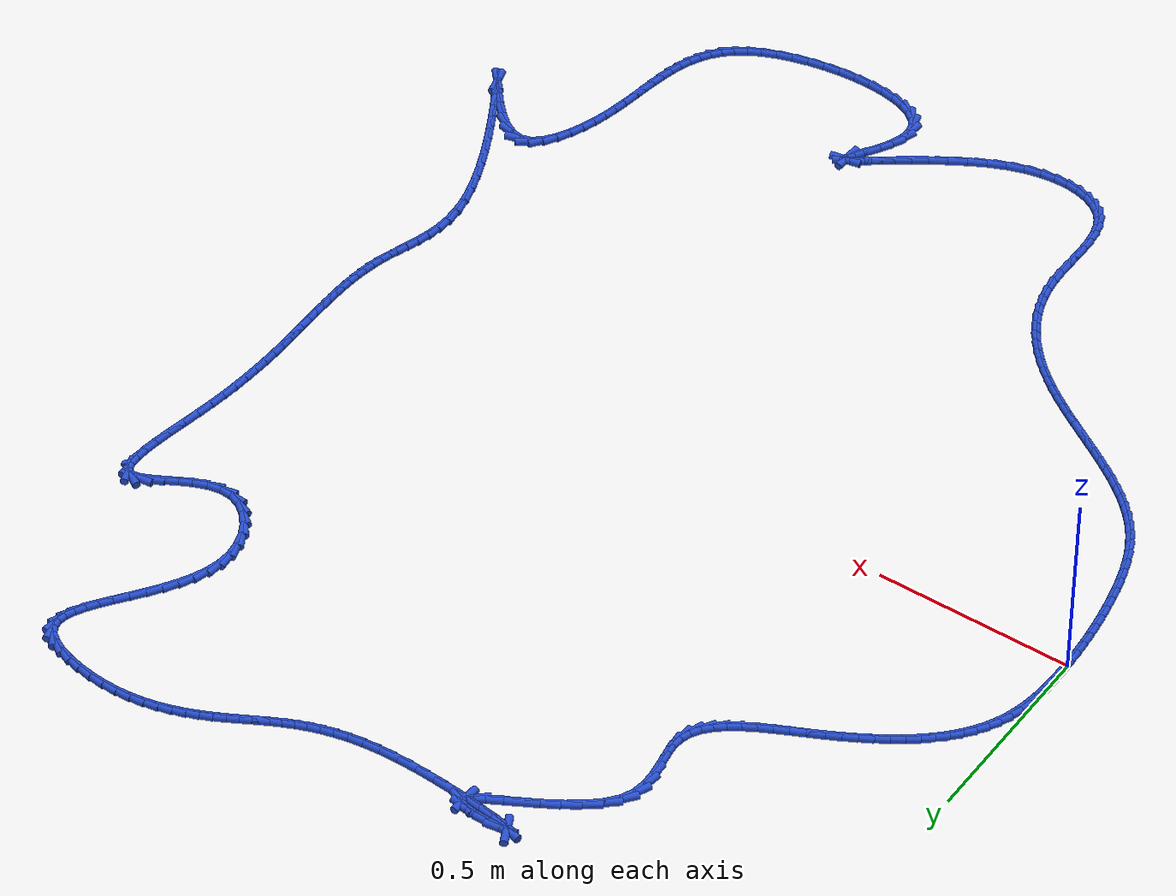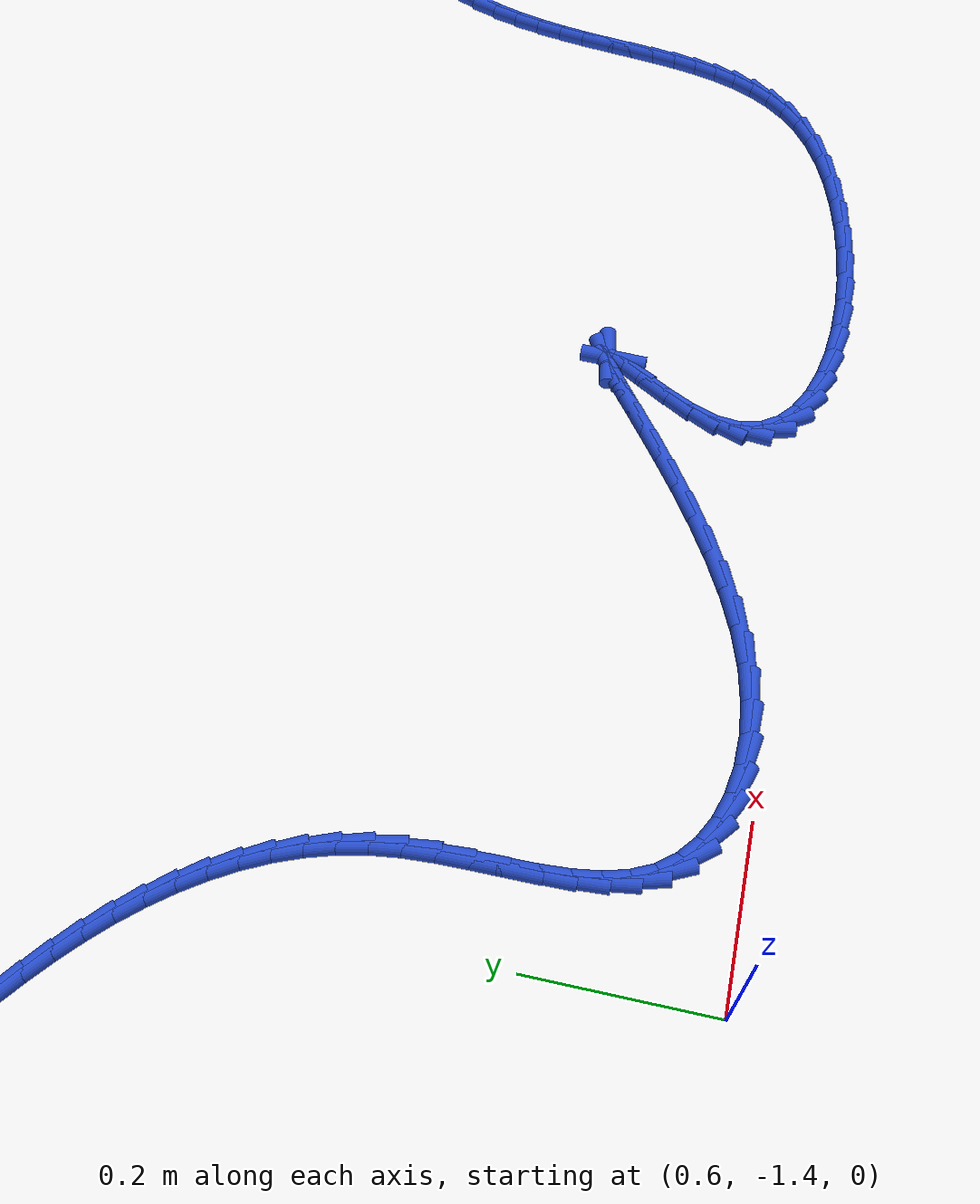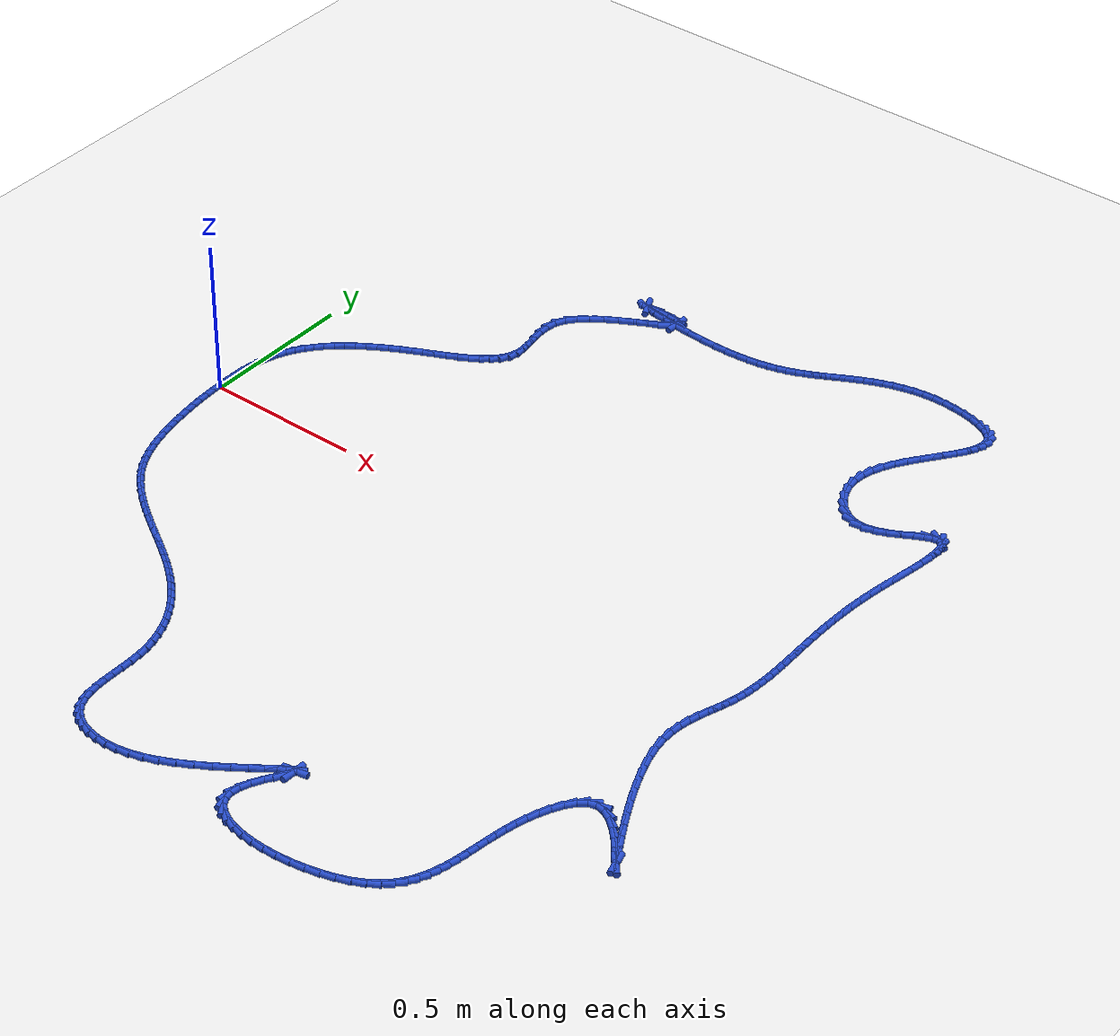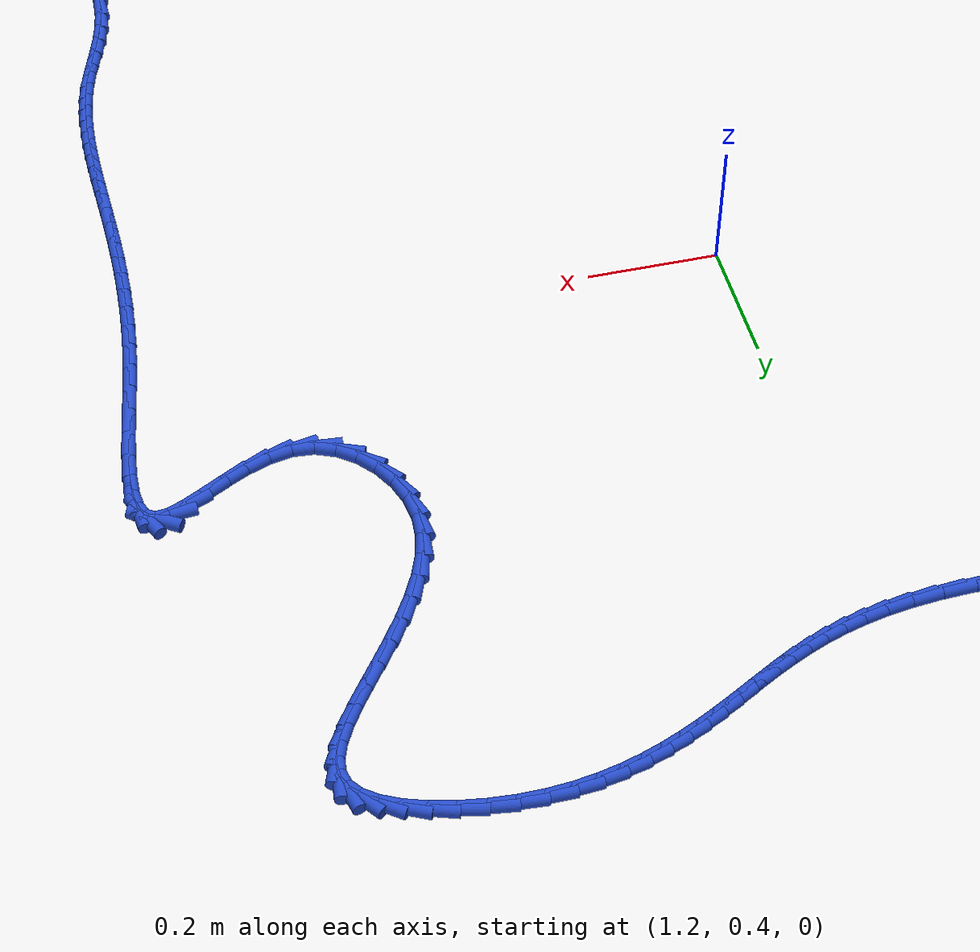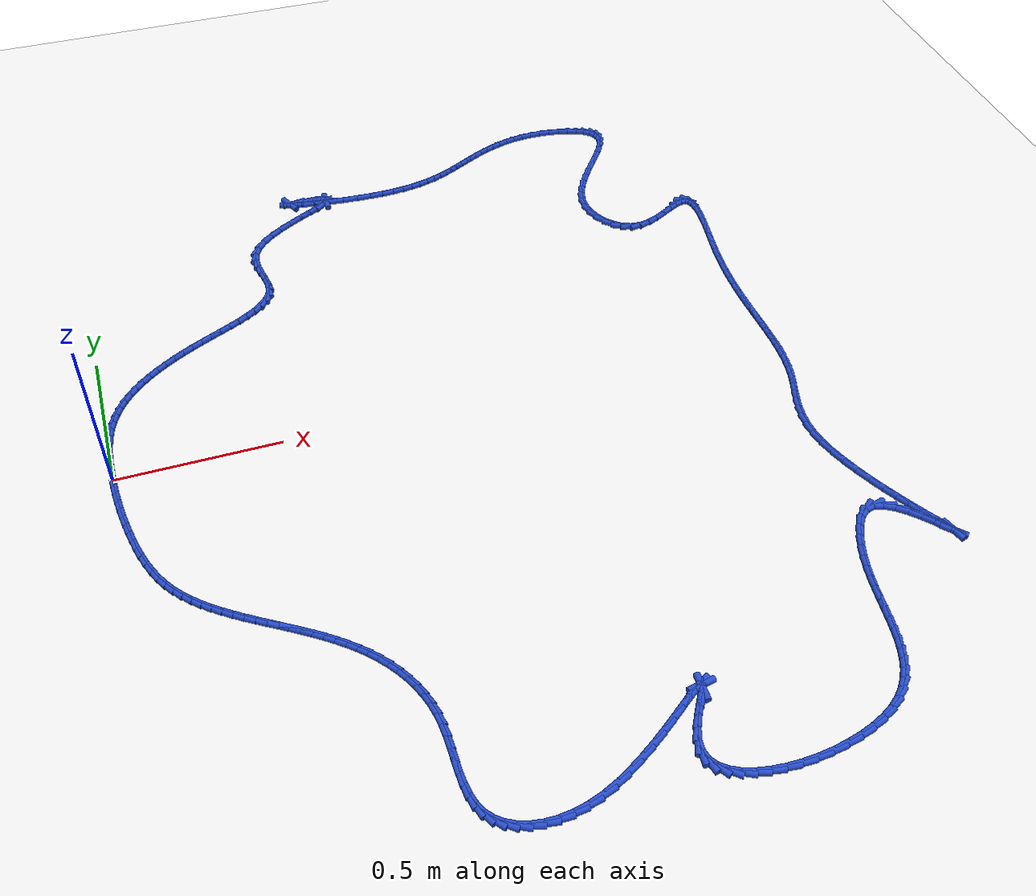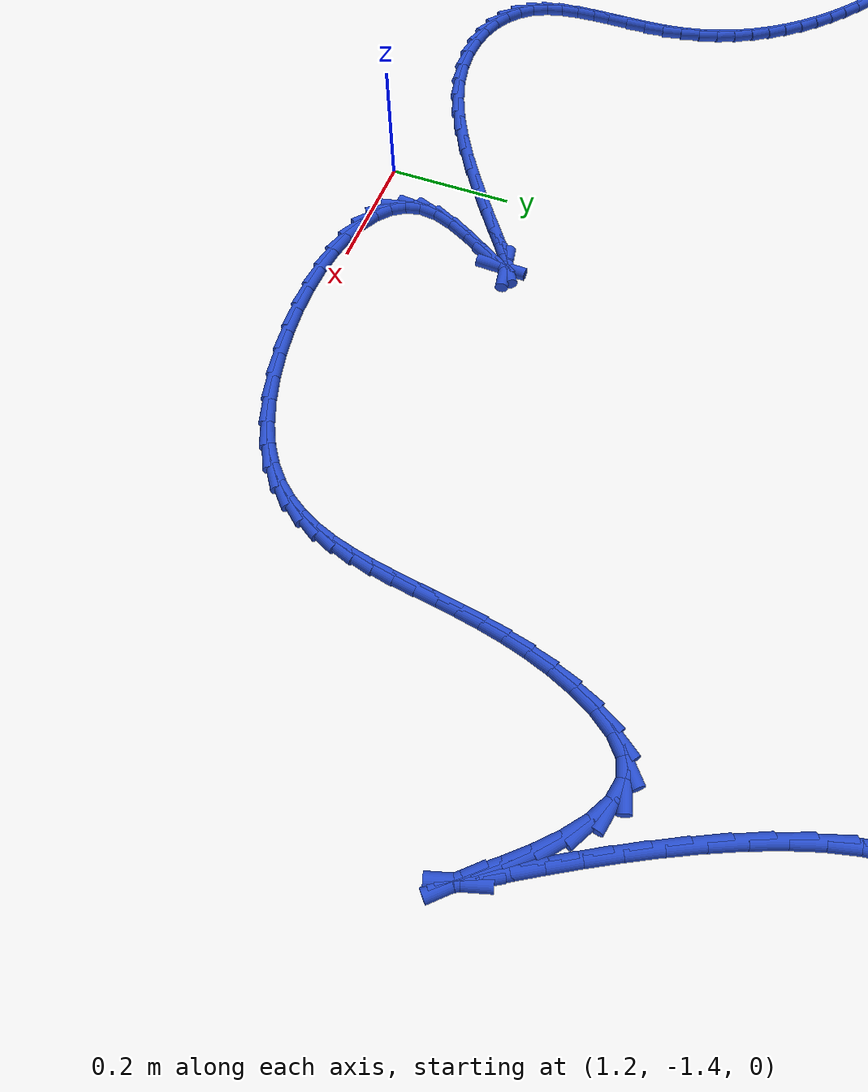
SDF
<sdf version="1.6">
 <world name="default">
  <light name="sun" type="directional">
   <pose>0 0 10 0 -0 0</pose>
   <diffuse>0.8 0.8 0.8 1</diffuse>
   <specular>0.2 0.2 0.2 1</specular>
   <attenuation>
    <range>1000</range>
    <constant>0.9</constant>
    <linear>0.01</linear>
    <quadratic>0.001</quadratic>
   </attenuation>
   <direction>-0.5 0.1 -0.9</direction>
  </light>
  <model name="ground_plane">
   <static>1</static>
   <link name="link">
    <collision name="collision">
     <geometry><plane><normal>0 0 1</normal><size>100 100</size></plane></geometry>
     <surface><friction><ode><mu>100</mu><mu2>50</mu2></ode></friction></surface>
    </collision>
    <visual name="visual">
     <cast_shadows>0</cast_shadows>
     <geometry><plane><normal>0 0 1</normal><size>100 100</size></plane></geometry>
     <material>
      <script><uri>file://media/materials/scripts/gazebo.material</uri><name>Gazebo/WhiteGlow</name></script>
     </material>
    </visual>
   </link>
  </model>
  <gravity>0 0 -9.8</gravity>
  <magnetic_field>6e-06 2.3e-05 -4.2e-05</magnetic_field>
  <atmosphere type="adiabatic"/>
  <physics name="default_physics" default="0" type="ode">
   <max_step_size>0.001</max_step_size>
   <real_time_factor>1</real_time_factor>
   <real_time_update_rate>1000</real_time_update_rate>
  </physics>
  <scene><ambient>0.4 0.4 0.4 1</ambient><background>0.7 0.7 0.7 1</background><shadows>1</shadows></scene>
  <spherical_coordinates>
   <surface_model>EARTH_WGS84</surface_model>
   <latitude_deg>0</latitude_deg>
   <longitude_deg>0</longitude_deg>
   <elevation>0</elevation>
   <heading_deg>0</heading_deg>
  </spherical_coordinates>
  <model name="line">
   <link name="link_0">
    <pose>1.1058862159352145e-17 -4.163336342344337e-17 0.01 0 1.57 -1.5520934585583777</pose>
    <collision name="collision">
     <geometry><cylinder><radius>0.01</radius><length>0.08</length></cylinder></geometry>
    </collision>
    <visual name="visual">
     <material>
      <script><name>Gazebo/Blue</name><uri>file://media/materials/scripts/gazebo.material</uri></script>
     </material>
     <geometry><cylinder><radius>0.01</radius><length>0.08</length></cylinder></geometry>
    </visual>
   </link>
   <link name="link_1">
    <pose>-0.0006060910726536685 0.03240253813865341 0.01 0 1.57 1.5602132643527702</pose>
    <collision name="collision">
     <geometry><cylinder><radius>0.01</radius><length>0.08</length></cylinder></geometry>
    </collision>
    <visual name="visual">
     <material>
      <script><name>Gazebo/Blue</name><uri>file://media/materials/scripts/gazebo.material</uri></script>
     </material>
     <geometry><cylinder><radius>0.01</radius><length>0.08</length></cylinder></geometry>
    </visual>
   </link>
   <link name="link_2">
    <pose>-0.00026167454089582134 0.06494545047513745 0.01 0 1.57 1.5225124292682661</pose>
    <collision name="collision">
     <geometry><cylinder><radius>0.01</radius><length>0.08</length></cylinder></geometry>
    </collision>
    <visual name="visual">
     <material>
      <script><name>Gazebo/Blue</name><uri>file://media/materials/scripts/gazebo.material</uri></script>
     </material>
     <geometry><cylinder><radius>0.01</radius><length>0.08</length></cylinder></geometry>
    </visual>
   </link>
   <link name="link_3">
    <pose>0.001304259534824519 0.09735205104350853 0.01 0 1.57 1.4754899106537582</pose>
    <collision name="collision">
     <geometry><cylinder><radius>0.01</radius><length>0.08</length></cylinder></geometry>
    </collision>
    <visual name="visual">
     <material>
      <script><name>Gazebo/Blue</name><uri>file://media/materials/scripts/gazebo.material</uri></script>
     </material>
     <geometry><cylinder><radius>0.01</radius><length>0.08</length></cylinder></geometry>
    </visual>
   </link>
   <link name="link_4">
    <pose>0.004362721094058318 0.12934565387782318 0.01 0 1.57 1.4179594097095918</pose>
    <collision name="collision">
     <geometry><cylinder><radius>0.01</radius><length>0.08</length></cylinder></geometry>
    </collision>
    <visual name="visual">
     <material>
      <script><name>Gazebo/Blue</name><uri>file://media/materials/scripts/gazebo.material</uri></script>
     </material>
     <geometry><cylinder><radius>0.01</radius><length>0.08</length></cylinder></geometry>
    </visual>
   </link>
   <link name="link_5">
    <pose>0.009184720076356545 0.160649573012138 0.01 0 1.57 1.3485221151968647</pose>
    <collision name="collision">
     <geometry><cylinder><radius>0.01</radius><length>0.08</length></cylinder></geometry>
    </collision>
    <visual name="visual">
     <material>
      <script><name>Gazebo/Blue</name><uri>file://media/materials/scripts/gazebo.material</uri></script>
     </material>
     <geometry><cylinder><radius>0.01</radius><length>0.08</length></cylinder></geometry>
    </visual>
   </link>
   <link name="link_6">
    <pose>0.016041266421270163 0.1909871224805094 0.01 0 1.57 1.2657338690753326</pose>
    <collision name="collision">
     <geometry><cylinder><radius>0.01</radius><length>0.08</length></cylinder></geometry>
    </collision>
    <visual name="visual">
     <material>
      <script><name>Gazebo/Blue</name><uri>file://media/materials/scripts/gazebo.material</uri></script>
     </material>
     <geometry><cylinder><radius>0.01</radius><length>0.08</length></cylinder></geometry>
    </visual>
   </link>
   <link name="link_7">
    <pose>0.025202995325985585 0.220081962973515 0.01 0 1.57 1.1728728424087764</pose>
    <collision name="collision">
     <geometry><cylinder><radius>0.01</radius><length>0.08</length></cylinder></geometry>
    </collision>
    <visual name="visual">
     <material>
      <script><name>Gazebo/Blue</name><uri>file://media/materials/scripts/gazebo.material</uri></script>
     </material>
     <geometry><cylinder><radius>0.01</radius><length>0.08</length></cylinder></geometry>
    </visual>
   </link>
   <link name="link_8">
    <pose>0.03683532720095613 0.24775508442811234 0.01 0 1.57 1.0810931739518155</pose>
    <collision name="collision">
     <geometry><cylinder><radius>0.01</radius><length>0.08</length></cylinder></geometry>
    </collision>
    <visual name="visual">
     <material>
      <script><name>Gazebo/Blue</name><uri>file://media/materials/scripts/gazebo.material</uri></script>
     </material>
     <geometry><cylinder><radius>0.01</radius><length>0.08</length></cylinder></geometry>
    </visual>
   </link>
   <link name="link_9">
    <pose>0.050854804195360606 0.27405770234519733 0.01 0 1.57 0.9936799867041609</pose>
    <collision name="collision">
     <geometry><cylinder><radius>0.01</radius><length>0.08</length></cylinder></geometry>
    </collision>
    <visual name="visual">
     <material>
      <script><name>Gazebo/Blue</name><uri>file://media/materials/scripts/gazebo.material</uri></script>
     </material>
     <geometry><cylinder><radius>0.01</radius><length>0.08</length></cylinder></geometry>
    </visual>
   </link>
   <link name="link_10">
    <pose>0.06714198887313642 0.2990743152462877 0.01 0 1.57 0.9120440300255599</pose>
    <collision name="collision">
     <geometry><cylinder><radius>0.01</radius><length>0.08</length></cylinder></geometry>
    </collision>
    <visual name="visual">
     <material>
      <script><name>Gazebo/Blue</name><uri>file://media/materials/scripts/gazebo.material</uri></script>
     </material>
     <geometry><cylinder><radius>0.01</radius><length>0.08</length></cylinder></geometry>
    </visual>
   </link>
   <link name="link_11">
    <pose>0.08557744379822098 0.3228894216529014 0.01 0 1.57 0.8371056735407433</pose>
    <collision name="collision">
     <geometry><cylinder><radius>0.01</radius><length>0.08</length></cylinder></geometry>
    </collision>
    <visual name="visual">
     <material>
      <script><name>Gazebo/Blue</name><uri>file://media/materials/scripts/gazebo.material</uri></script>
     </material>
     <geometry><cylinder><radius>0.01</radius><length>0.08</length></cylinder></geometry>
    </visual>
   </link>
   <link name="link_12">
    <pose>0.10604173153455172 0.34558752008655674 0.01 0 1.57 0.769320851371035</pose>
    <collision name="collision">
     <geometry><cylinder><radius>0.01</radius><length>0.08</length></cylinder></geometry>
    </collision>
    <visual name="visual">
     <material>
      <script><name>Gazebo/Blue</name><uri>file://media/materials/scripts/gazebo.material</uri></script>
     </material>
     <geometry><cylinder><radius>0.01</radius><length>0.08</length></cylinder></geometry>
    </visual>
   </link>
   <link name="link_13">
    <pose>0.1284154146460661 0.36725310906877157 0.01 0 1.57 0.7087666705866533</pose>
    <collision name="collision">
     <geometry><cylinder><radius>0.01</radius><length>0.08</length></cylinder></geometry>
    </collision>
    <visual name="visual">
     <material>
      <script><name>Gazebo/Blue</name><uri>file://media/materials/scripts/gazebo.material</uri></script>
     </material>
     <geometry><cylinder><radius>0.01</radius><length>0.08</length></cylinder></geometry>
    </visual>
   </link>
   <link name="link_14">
    <pose>0.15257905569670144 0.3879706871210638 0.01 0 1.57 0.6552488280356645</pose>
    <collision name="collision">
     <geometry><cylinder><radius>0.01</radius><length>0.08</length></cylinder></geometry>
    </collision>
    <visual name="visual">
     <material>
      <script><name>Gazebo/Blue</name><uri>file://media/materials/scripts/gazebo.material</uri></script>
     </material>
     <geometry><cylinder><radius>0.01</radius><length>0.08</length></cylinder></geometry>
    </visual>
   </link>
   <link name="link_15">
    <pose>0.17841321725039522 0.40782475276495145 0.01 0 1.57 0.6084033217376213</pose>
    <collision name="collision">
     <geometry><cylinder><radius>0.01</radius><length>0.08</length></cylinder></geometry>
    </collision>
    <visual name="visual">
     <material>
      <script><name>Gazebo/Blue</name><uri>file://media/materials/scripts/gazebo.material</uri></script>
     </material>
     <geometry><cylinder><radius>0.01</radius><length>0.08</length></cylinder></geometry>
    </visual>
   </link>
   <link name="link_16">
    <pose>0.2057984618710848 0.4268998045219526 0.01 0 1.57 0.5677786259152287</pose>
    <collision name="collision">
     <geometry><cylinder><radius>0.01</radius><length>0.08</length></cylinder></geometry>
    </collision>
    <visual name="visual">
     <material>
      <script><name>Gazebo/Blue</name><uri>file://media/materials/scripts/gazebo.material</uri></script>
     </material>
     <geometry><cylinder><radius>0.01</radius><length>0.08</length></cylinder></geometry>
    </visual>
   </link>
   <link name="link_17">
    <pose>0.23461535212270768 0.44528034091358515 0.01 0 1.57 0.532895030632407</pose>
    <collision name="collision">
     <geometry><cylinder><radius>0.01</radius><length>0.08</length></cylinder></geometry>
    </collision>
    <visual name="visual">
     <material>
      <script><name>Gazebo/Blue</name><uri>file://media/materials/scripts/gazebo.material</uri></script>
     </material>
     <geometry><cylinder><radius>0.01</radius><length>0.08</length></cylinder></geometry>
    </visual>
   </link>
   <link name="link_18">
    <pose>0.26474445056920126 0.46305086046136723 0.01 0 1.57 0.5032836581255119</pose>
    <collision name="collision">
     <geometry><cylinder><radius>0.01</radius><length>0.08</length></cylinder></geometry>
    </collision>
    <visual name="visual">
     <material>
      <script><name>Gazebo/Blue</name><uri>file://media/materials/scripts/gazebo.material</uri></script>
     </material>
     <geometry><cylinder><radius>0.01</radius><length>0.08</length></cylinder></geometry>
    </visual>
   </link>
   <link name="link_19">
    <pose>0.2960663197745028 0.48029586168681676 0.01 0 1.57 0.4785097959581657</pose>
    <collision name="collision">
     <geometry><cylinder><radius>0.01</radius><length>0.08</length></cylinder></geometry>
    </collision>
    <visual name="visual">
     <material>
      <script><name>Gazebo/Blue</name><uri>file://media/materials/scripts/gazebo.material</uri></script>
     </material>
     <geometry><cylinder><radius>0.01</radius><length>0.08</length></cylinder></geometry>
    </visual>
   </link>
   <link name="link_20">
    <pose>0.32846152230255 0.4970998431114516 0.01 0 1.57 0.45835798372783104</pose>
    <collision name="collision">
     <geometry><cylinder><radius>0.01</radius><length>0.08</length></cylinder></geometry>
    </collision>
    <visual name="visual">
     <material>
      <script><name>Gazebo/Blue</name><uri>file://media/materials/scripts/gazebo.material</uri></script>
     </material>
     <geometry><cylinder><radius>0.01</radius><length>0.08</length></cylinder></geometry>
    </visual>
   </link>
   <link name="link_21">
    <pose>0.36180171199137373 0.5135500710245826 0.01 0 1.57 0.44833628615228893</pose>
    <collision name="collision">
     <geometry><cylinder><radius>0.01</radius><length>0.08</length></cylinder></geometry>
    </collision>
    <visual name="visual">
     <material>
      <script><name>Gazebo/Blue</name><uri>file://media/materials/scripts/gazebo.material</uri></script>
     </material>
     <geometry><cylinder><radius>0.01</radius><length>0.08</length></cylinder></geometry>
    </visual>
   </link>
   <link name="link_22">
    <pose>0.395647992219943 0.5298302937004354 0.01 0 1.57 0.45522385149832384</pose>
    <collision name="collision">
     <geometry><cylinder><radius>0.01</radius><length>0.08</length></cylinder></geometry>
    </collision>
    <visual name="visual">
     <material>
      <script><name>Gazebo/Blue</name><uri>file://media/materials/scripts/gazebo.material</uri></script>
     </material>
     <geometry><cylinder><radius>0.01</radius><length>0.08</length></cylinder></geometry>
    </visual>
   </link>
   <link name="link_23">
    <pose>0.4291776071566356 0.5462435170008046 0.01 0 1.57 0.4801533569906769</pose>
    <collision name="collision">
     <geometry><cylinder><radius>0.01</radius><length>0.08</length></cylinder></geometry>
    </collision>
    <visual name="visual">
     <material>
      <script><name>Gazebo/Blue</name><uri>file://media/materials/scripts/gazebo.material</uri></script>
     </material>
     <geometry><cylinder><radius>0.01</radius><length>0.08</length></cylinder></geometry>
    </visual>
   </link>
   <link name="link_24">
    <pose>0.46154402375373493 0.563100133905867 0.01 0 1.57 0.525670705203946</pose>
    <collision name="collision">
     <geometry><cylinder><radius>0.01</radius><length>0.08</length></cylinder></geometry>
    </collision>
    <visual name="visual">
     <material>
      <script><name>Gazebo/Blue</name><uri>file://media/materials/scripts/gazebo.material</uri></script>
     </material>
     <geometry><cylinder><radius>0.01</radius><length>0.08</length></cylinder></geometry>
    </visual>
   </link>
   <link name="link_25">
    <pose>0.4919007089635234 0.5807105373957983 0.01 0 1.57 0.596537264560504</pose>
    <collision name="collision">
     <geometry><cylinder><radius>0.01</radius><length>0.08</length></cylinder></geometry>
    </collision>
    <visual name="visual">
     <material>
      <script><name>Gazebo/Blue</name><uri>file://media/materials/scripts/gazebo.material</uri></script>
     </material>
     <geometry><cylinder><radius>0.01</radius><length>0.08</length></cylinder></geometry>
    </visual>
   </link>
   <link name="link_26">
    <pose>0.5194011297382842 0.599385120450775 0.01 0 1.57 0.7001153752594739</pose>
    <collision name="collision">
     <geometry><cylinder><radius>0.01</radius><length>0.08</length></cylinder></geometry>
    </collision>
    <visual name="visual">
     <material>
      <script><name>Gazebo/Blue</name><uri>file://media/materials/scripts/gazebo.material</uri></script>
     </material>
     <geometry><cylinder><radius>0.01</radius><length>0.08</length></cylinder></geometry>
    </visual>
   </link>
   <link name="link_27">
    <pose>0.5431987530303005 0.6194342760509737 0.01 0 1.57 0.8459799169875396</pose>
    <collision name="collision">
     <geometry><cylinder><radius>0.01</radius><length>0.08</length></cylinder></geometry>
    </collision>
    <visual name="visual">
     <material>
      <script><name>Gazebo/Blue</name><uri>file://media/materials/scripts/gazebo.material</uri></script>
     </material>
     <geometry><cylinder><radius>0.01</radius><length>0.08</length></cylinder></geometry>
    </visual>
   </link>
   <link name="link_28">
    <pose>0.5624470457918553 0.6411683971765703 0.01 0 1.57 1.0424001961573721</pose>
    <collision name="collision">
     <geometry><cylinder><radius>0.01</radius><length>0.08</length></cylinder></geometry>
    </collision>
    <visual name="visual">
     <material>
      <script><name>Gazebo/Blue</name><uri>file://media/materials/scripts/gazebo.material</uri></script>
     </material>
     <geometry><cylinder><radius>0.01</radius><length>0.08</length></cylinder></geometry>
    </visual>
   </link>
   <link name="link_29">
    <pose>0.5762994749752313 0.6648978768077413 0.01 0 1.57 1.2864209547235084</pose>
    <collision name="collision">
     <geometry><cylinder><radius>0.01</radius><length>0.08</length></cylinder></geometry>
    </collision>
    <visual name="visual">
     <material>
      <script><name>Gazebo/Blue</name><uri>file://media/materials/scripts/gazebo.material</uri></script>
     </material>
     <geometry><cylinder><radius>0.01</radius><length>0.08</length></cylinder></geometry>
    </visual>
   </link>
   <link name="link_30">
    <pose>0.583909507532712 0.690933107924663 0.01 0 1.57 1.5363271752811638</pose>
    <collision name="collision">
     <geometry><cylinder><radius>0.01</radius><length>0.08</length></cylinder></geometry>
    </collision>
    <visual name="visual">
     <material>
      <script><name>Gazebo/Blue</name><uri>file://media/materials/scripts/gazebo.material</uri></script>
     </material>
     <geometry><cylinder><radius>0.01</radius><length>0.08</length></cylinder></geometry>
    </visual>
   </link>
   <link name="link_31">
    <pose>0.5848933159905345 0.7194635113572749 0.01 0 1.57 -1.451289024398585</pose>
    <collision name="collision">
     <geometry><cylinder><radius>0.01</radius><length>0.08</length></cylinder></geometry>
    </collision>
    <visual name="visual">
     <material>
      <script><name>Gazebo/Blue</name><uri>file://media/materials/scripts/gazebo.material</uri></script>
     </material>
     <geometry><cylinder><radius>0.01</radius><length>0.08</length></cylinder></geometry>
    </visual>
   </link>
   <link name="link_32">
    <pose>0.5812188673597649 0.7500636425615945 0.01 0 1.57 -1.3972261909447563</pose>
    <collision name="collision">
     <geometry><cylinder><radius>0.01</radius><length>0.08</length></cylinder></geometry>
    </collision>
    <visual name="visual">
     <material>
      <script><name>Gazebo/Blue</name><uri>file://media/materials/scripts/gazebo.material</uri></script>
     </material>
     <geometry><cylinder><radius>0.01</radius><length>0.08</length></cylinder></geometry>
    </visual>
   </link>
   <link name="link_33">
    <pose>0.575599478583929 0.7821131888332284 0.01 0 1.57 -1.4243188001058744</pose>
    <collision name="collision">
     <geometry><cylinder><radius>0.01</radius><length>0.08</length></cylinder></geometry>
    </collision>
    <visual name="visual">
     <material>
      <script><name>Gazebo/Blue</name><uri>file://media/materials/scripts/gazebo.material</uri></script>
     </material>
     <geometry><cylinder><radius>0.01</radius><length>0.08</length></cylinder></geometry>
    </visual>
   </link>
   <link name="link_34">
    <pose>0.5707487654097537 0.8149917593471208 0.01 0 1.57 -1.5294618457765954</pose>
    <collision name="collision">
     <geometry><cylinder><radius>0.01</radius><length>0.08</length></cylinder></geometry>
    </collision>
    <visual name="visual">
     <material>
      <script><name>Gazebo/Blue</name><uri>file://media/materials/scripts/gazebo.material</uri></script>
     </material>
     <geometry><cylinder><radius>0.01</radius><length>0.08</length></cylinder></geometry>
    </visual>
   </link>
   <link name="link_35">
    <pose>0.5693803435839668 0.8480789632782162 0.01 0 1.57 1.4241169343037612</pose>
    <collision name="collision">
     <geometry><cylinder><radius>0.01</radius><length>0.08</length></cylinder></geometry>
    </collision>
    <visual name="visual">
     <material>
      <script><name>Gazebo/Blue</name><uri>file://media/materials/scripts/gazebo.material</uri></script>
     </material>
     <geometry><cylinder><radius>0.01</radius><length>0.08</length></cylinder></geometry>
    </visual>
   </link>
   <link name="link_36">
    <pose>0.574207828853295 0.8807544098014592 0.01 0 1.57 1.1613604403302198</pose>
    <collision name="collision">
     <geometry><cylinder><radius>0.01</radius><length>0.08</length></cylinder></geometry>
    </collision>
    <visual name="visual">
     <material>
      <script><name>Gazebo/Blue</name><uri>file://media/materials/scripts/gazebo.material</uri></script>
     </material>
     <geometry><cylinder><radius>0.01</radius><length>0.08</length></cylinder></geometry>
    </visual>
   </link>
   <link name="link_37">
    <pose>0.5879399685412801 0.9123981506826963 0.01 0 1.57 0.8999026367714584</pose>
    <collision name="collision">
     <geometry><cylinder><radius>0.01</radius><length>0.08</length></cylinder></geometry>
    </collision>
    <visual name="visual">
     <material>
      <script><name>Gazebo/Blue</name><uri>file://media/materials/scripts/gazebo.material</uri></script>
     </material>
     <geometry><cylinder><radius>0.01</radius><length>0.08</length></cylinder></geometry>
    </visual>
   </link>
   <link name="link_38">
    <pose>0.6118486610744582 0.9425208623737005 0.01 0 1.57 0.7274534972356197</pose>
    <collision name="collision">
     <geometry><cylinder><radius>0.01</radius><length>0.08</length></cylinder></geometry>
    </collision>
    <visual name="visual">
     <material>
      <script><name>Gazebo/Blue</name><uri>file://media/materials/scripts/gazebo.material</uri></script>
     </material>
     <geometry><cylinder><radius>0.01</radius><length>0.08</length></cylinder></geometry>
    </visual>
   </link>
   <link name="link_39">
    <pose>0.643773873415388 0.9709452200134729 0.01 0 1.57 0.6196383089457602</pose>
    <collision name="collision">
     <geometry><cylinder><radius>0.01</radius><length>0.08</length></cylinder></geometry>
    </collision>
    <visual name="visual">
     <material>
      <script><name>Gazebo/Blue</name><uri>file://media/materials/scripts/gazebo.material</uri></script>
     </material>
     <geometry><cylinder><radius>0.01</radius><length>0.08</length></cylinder></geometry>
    </visual>
   </link>
   <link name="link_40">
    <pose>0.6810540120918513 0.9975394958628835 0.01 0 1.57 0.5522609275304683</pose>
    <collision name="collision">
     <geometry><cylinder><radius>0.01</radius><length>0.08</length></cylinder></geometry>
    </collision>
    <visual name="visual">
     <material>
      <script><name>Gazebo/Blue</name><uri>file://media/materials/scripts/gazebo.material</uri></script>
     </material>
     <geometry><cylinder><radius>0.01</radius><length>0.08</length></cylinder></geometry>
    </visual>
   </link>
   <link name="link_41">
    <pose>0.7210274836316295 1.0221719621828025 0.01 0 1.57 0.513072748128519</pose>
    <collision name="collision">
     <geometry><cylinder><radius>0.01</radius><length>0.08</length></cylinder></geometry>
    </collision>
    <visual name="visual">
     <material>
      <script><name>Gazebo/Blue</name><uri>file://media/materials/scripts/gazebo.material</uri></script>
     </material>
     <geometry><cylinder><radius>0.01</radius><length>0.08</length></cylinder></geometry>
    </visual>
   </link>
   <link name="link_42">
    <pose>0.7610326945625043 1.0447108912340999 0.01 0 1.57 0.4978423697049908</pose>
    <collision name="collision">
     <geometry><cylinder><radius>0.01</radius><length>0.08</length></cylinder></geometry>
    </collision>
    <visual name="visual">
     <material>
      <script><name>Gazebo/Blue</name><uri>file://media/materials/scripts/gazebo.material</uri></script>
     </material>
     <geometry><cylinder><radius>0.01</radius><length>0.08</length></cylinder></geometry>
    </visual>
   </link>
   <link name="link_43">
    <pose>0.7984080514122573 1.0650245552776458 0.01 0 1.57 0.5102434715136569</pose>
    <collision name="collision">
     <geometry><cylinder><radius>0.01</radius><length>0.08</length></cylinder></geometry>
    </collision>
    <visual name="visual">
     <material>
      <script><name>Gazebo/Blue</name><uri>file://media/materials/scripts/gazebo.material</uri></script>
     </material>
     <geometry><cylinder><radius>0.01</radius><length>0.08</length></cylinder></geometry>
    </visual>
   </link>
   <link name="link_44">
    <pose>0.830491960708671 1.0829812265743113 0.01 0 1.57 0.5700241772763422</pose>
    <collision name="collision">
     <geometry><cylinder><radius>0.01</radius><length>0.08</length></cylinder></geometry>
    </collision>
    <visual name="visual">
     <material>
      <script><name>Gazebo/Blue</name><uri>file://media/materials/scripts/gazebo.material</uri></script>
     </material>
     <geometry><cylinder><radius>0.01</radius><length>0.08</length></cylinder></geometry>
    </visual>
   </link>
   <link name="link_45">
    <pose>0.8546228289795263 1.0984491773849665 0.01 0 1.57 0.7600380319440292</pose>
    <collision name="collision">
     <geometry><cylinder><radius>0.01</radius><length>0.08</length></cylinder></geometry>
    </collision>
    <visual name="visual">
     <material>
      <script><name>Gazebo/Blue</name><uri>file://media/materials/scripts/gazebo.material</uri></script>
     </material>
     <geometry><cylinder><radius>0.01</radius><length>0.08</length></cylinder></geometry>
    </visual>
   </link>
   <link name="link_46">
    <pose>0.8681390627526052 1.111296679970481 0.01 0 1.57 1.5470268530313165</pose>
    <collision name="collision">
     <geometry><cylinder><radius>0.01</radius><length>0.08</length></cylinder></geometry>
    </collision>
    <visual name="visual">
     <material>
      <script><name>Gazebo/Blue</name><uri>file://media/materials/scripts/gazebo.material</uri></script>
     </material>
     <geometry><cylinder><radius>0.01</radius><length>0.08</length></cylinder></geometry>
    </visual>
   </link>
   <link name="link_47">
    <pose>0.8683790685556898 1.1213920065917264 0.01 0 1.57 -0.4308130709094269</pose>
    <collision name="collision">
     <geometry><cylinder><radius>0.01</radius><length>0.08</length></cylinder></geometry>
    </collision>
    <visual name="visual">
     <material>
      <script><name>Gazebo/Blue</name><uri>file://media/materials/scripts/gazebo.material</uri></script>
     </material>
     <geometry><cylinder><radius>0.01</radius><length>0.08</length></cylinder></geometry>
    </visual>
   </link>
   <link name="link_48">
    <pose>0.8526880776541562 1.1286036719582224 0.01 0 1.57 -0.1391327244283233</pose>
    <collision name="collision">
     <geometry><cylinder><radius>0.01</radius><length>0.08</length></cylinder></geometry>
    </collision>
    <visual name="visual">
     <material>
      <script><name>Gazebo/Blue</name><uri>file://media/materials/scripts/gazebo.material</uri></script>
     </material>
     <geometry><cylinder><radius>0.01</radius><length>0.08</length></cylinder></geometry>
    </visual>
   </link>
   <link name="link_49">
    <pose>0.8218489156038112 1.1329223112398301 0.01 0 1.57 -0.04793167152168271</pose>
    <collision name="collision">
     <geometry><cylinder><radius>0.01</radius><length>0.08</length></cylinder></geometry>
    </collision>
    <visual name="visual">
     <material>
      <script><name>Gazebo/Blue</name><uri>file://media/materials/scripts/gazebo.material</uri></script>
     </material>
     <geometry><cylinder><radius>0.01</radius><length>0.08</length></cylinder></geometry>
    </visual>
   </link>
   <link name="link_50">
    <pose>0.785652786784137 1.1346585820627892 0.01 0 1.57 0.015958697669039228</pose>
    <collision name="collision">
     <geometry><cylinder><radius>0.01</radius><length>0.08</length></cylinder></geometry>
    </collision>
    <visual name="visual">
     <material>
      <script><name>Gazebo/Blue</name><uri>file://media/materials/scripts/gazebo.material</uri></script>
     </material>
     <geometry><cylinder><radius>0.01</radius><length>0.08</length></cylinder></geometry>
    </visual>
   </link>
   <link name="link_51">
    <pose>0.7553485324001632 1.1341749245689907 0.01 0 1.57 0.15794410453557198</pose>
    <collision name="collision">
     <geometry><cylinder><radius>0.01</radius><length>0.08</length></cylinder></geometry>
    </collision>
    <visual name="visual">
     <material>
      <script><name>Gazebo/Blue</name><uri>file://media/materials/scripts/gazebo.material</uri></script>
     </material>
     <geometry><cylinder><radius>0.01</radius><length>0.08</length></cylinder></geometry>
    </visual>
   </link>
   <link name="link_52">
    <pose>0.7406864272374709 1.1318396805292927 0.01 0 1.57 -1.1145672192782712</pose>
    <collision name="collision">
     <geometry><cylinder><radius>0.01</radius><length>0.08</length></cylinder></geometry>
    </collision>
    <visual name="visual">
     <material>
      <script><name>Gazebo/Blue</name><uri>file://media/materials/scripts/gazebo.material</uri></script>
     </material>
     <geometry><cylinder><radius>0.01</radius><length>0.08</length></cylinder></geometry>
    </visual>
   </link>
   <link name="link_53">
    <pose>0.7425432426471108 1.1280561371959426 0.01 0 1.57 -0.2923841487421327</pose>
    <collision name="collision">
     <geometry><cylinder><radius>0.01</radius><length>0.08</length></cylinder></geometry>
    </collision>
    <visual name="visual">
     <material>
      <script><name>Gazebo/Blue</name><uri>file://media/materials/scripts/gazebo.material</uri></script>
     </material>
     <geometry><cylinder><radius>0.01</radius><length>0.08</length></cylinder></geometry>
    </visual>
   </link>
   <link name="link_54">
    <pose>0.7585417912916206 1.1232403965063458 0.01 0 1.57 -0.1932417491703598</pose>
    <collision name="collision">
     <geometry><cylinder><radius>0.01</radius><length>0.08</length></cylinder></geometry>
    </collision>
    <visual name="visual">
     <material>
      <script><name>Gazebo/Blue</name><uri>file://media/materials/scripts/gazebo.material</uri></script>
     </material>
     <geometry><cylinder><radius>0.01</radius><length>0.08</length></cylinder></geometry>
    </visual>
   </link>
   <link name="link_55">
    <pose>0.7862999515703305 1.117808579829942 0.01 0 1.57 -0.15050719407081997</pose>
    <collision name="collision">
     <geometry><cylinder><radius>0.01</radius><length>0.08</length></cylinder></geometry>
    </collision>
    <visual name="visual">
     <material>
      <script><name>Gazebo/Blue</name><uri>file://media/materials/scripts/gazebo.material</uri></script>
     </material>
     <geometry><cylinder><radius>0.01</radius><length>0.08</length></cylinder></geometry>
    </visual>
   </link>
   <link name="link_56">
    <pose>0.8234356018825693 1.1121768085361694 0.01 0 1.57 -0.12210600551469747</pose>
    <collision name="collision">
     <geometry><cylinder><radius>0.01</radius><length>0.08</length></cylinder></geometry>
    </collision>
    <visual name="visual">
     <material>
      <script><name>Gazebo/Blue</name><uri>file://media/materials/scripts/gazebo.material</uri></script>
     </material>
     <geometry><cylinder><radius>0.01</radius><length>0.08</length></cylinder></geometry>
    </visual>
   </link>
   <link name="link_57">
    <pose>0.8675666206276664 1.1067612039944672 0.01 0 1.57 -0.09781767268450549</pose>
    <collision name="collision">
     <geometry><cylinder><radius>0.01</radius><length>0.08</length></cylinder></geometry>
    </collision>
    <visual name="visual">
     <material>
      <script><name>Gazebo/Blue</name><uri>file://media/materials/scripts/gazebo.material</uri></script>
     </material>
     <geometry><cylinder><radius>0.01</radius><length>0.08</length></cylinder></geometry>
    </visual>
   </link>
   <link name="link_58">
    <pose>0.9163108862049509 1.1019778875742745 0.01 0 1.57 -0.07313813435281924</pose>
    <collision name="collision">
     <geometry><cylinder><radius>0.01</radius><length>0.08</length></cylinder></geometry>
    </collision>
    <visual name="visual">
     <material>
      <script><name>Gazebo/Blue</name><uri>file://media/materials/scripts/gazebo.material</uri></script>
     </material>
     <geometry><cylinder><radius>0.01</radius><length>0.08</length></cylinder></geometry>
    </visual>
   </link>
   <link name="link_59">
    <pose>0.967286277013752 1.09824298064503 0.01 0 1.57 -0.04464131295387199</pose>
    <collision name="collision">
     <geometry><cylinder><radius>0.01</radius><length>0.08</length></cylinder></geometry>
    </collision>
    <visual name="visual">
     <material>
      <script><name>Gazebo/Blue</name><uri>file://media/materials/scripts/gazebo.material</uri></script>
     </material>
     <geometry><cylinder><radius>0.01</radius><length>0.08</length></cylinder></geometry>
    </visual>
   </link>
   <link name="link_60">
    <pose>1.0181106714533994 1.0959726045761724 0.01 0 1.57 -0.008094579615655607</pose>
    <collision name="collision">
     <geometry><cylinder><radius>0.01</radius><length>0.08</length></cylinder></geometry>
    </collision>
    <visual name="visual">
     <material>
      <script><name>Gazebo/Blue</name><uri>file://media/materials/scripts/gazebo.material</uri></script>
     </material>
     <geometry><cylinder><radius>0.01</radius><length>0.08</length></cylinder></geometry>
    </visual>
   </link>
   <link name="link_61">
    <pose>1.0664076326705691 1.0955816524396846 0.01 0 1.57 0.038887482790159314</pose>
    <collision name="collision">
     <geometry><cylinder><radius>0.01</radius><length>0.08</length></cylinder></geometry>
    </collision>
    <visual name="visual">
     <material>
      <script><name>Gazebo/Blue</name><uri>file://media/materials/scripts/gazebo.material</uri></script>
     </material>
     <geometry><cylinder><radius>0.01</radius><length>0.08</length></cylinder></geometry>
    </visual>
   </link>
   <link name="link_62">
    <pose>1.1106441977543198 1.0973027687687595 0.01 0 1.57 0.09119885731816915</pose>
    <collision name="collision">
     <geometry><cylinder><radius>0.01</radius><length>0.08</length></cylinder></geometry>
    </collision>
    <visual name="visual">
     <material>
      <script><name>Gazebo/Blue</name><uri>file://media/materials/scripts/gazebo.material</uri></script>
     </material>
     <geometry><cylinder><radius>0.01</radius><length>0.08</length></cylinder></geometry>
    </visual>
   </link>
   <link name="link_63">
    <pose>1.1510167459639884 1.1009949409297635 0.01 0 1.57 0.1472698020350449</pose>
    <collision name="collision">
     <geometry><cylinder><radius>0.01</radius><length>0.08</length></cylinder></geometry>
    </collision>
    <visual name="visual">
     <material>
      <script><name>Gazebo/Blue</name><uri>file://media/materials/scripts/gazebo.material</uri></script>
     </material>
     <geometry><cylinder><radius>0.01</radius><length>0.08</length></cylinder></geometry>
    </visual>
   </link>
   <link name="link_64">
    <pose>1.187933694583317 1.1064713414533276 0.01 0 1.57 0.2058933623002084</pose>
    <collision name="collision">
     <geometry><cylinder><radius>0.01</radius><length>0.08</length></cylinder></geometry>
    </collision>
    <visual name="visual">
     <material>
      <script><name>Gazebo/Blue</name><uri>file://media/materials/scripts/gazebo.material</uri></script>
     </material>
     <geometry><cylinder><radius>0.01</radius><length>0.08</length></cylinder></geometry>
    </visual>
   </link>
   <link name="link_65">
    <pose>1.2218034608960486 1.113545142870085 0.01 0 1.57 0.2652631973887757</pose>
    <collision name="collision">
     <geometry><cylinder><radius>0.01</radius><length>0.08</length></cylinder></geometry>
    </collision>
    <visual name="visual">
     <material>
      <script><name>Gazebo/Blue</name><uri>file://media/materials/scripts/gazebo.material</uri></script>
     </material>
     <geometry><cylinder><radius>0.01</radius><length>0.08</length></cylinder></geometry>
    </visual>
   </link>
   <link name="link_66">
    <pose>1.253034462185925 1.122029517710668 0.01 0 1.57 0.32302972576154204</pose>
    <collision name="collision">
     <geometry><cylinder><radius>0.01</radius><length>0.08</length></cylinder></geometry>
    </collision>
    <visual name="visual">
     <material>
      <script><name>Gazebo/Blue</name><uri>file://media/materials/scripts/gazebo.material</uri></script>
     </material>
     <geometry><cylinder><radius>0.01</radius><length>0.08</length></cylinder></geometry>
    </visual>
   </link>
   <link name="link_67">
    <pose>1.2820351157366898 1.1317376385057092 0.01 0 1.57 0.37648914779969817</pose>
    <collision name="collision">
     <geometry><cylinder><radius>0.01</radius><length>0.08</length></cylinder></geometry>
    </collision>
    <visual name="visual">
     <material>
      <script><name>Gazebo/Blue</name><uri>file://media/materials/scripts/gazebo.material</uri></script>
     </material>
     <geometry><cylinder><radius>0.01</radius><length>0.08</length></cylinder></geometry>
    </visual>
   </link>
   <link name="link_68">
    <pose>1.309213838832085 1.1424826777858401 0.01 0 1.57 0.422879289386558</pose>
    <collision name="collision">
     <geometry><cylinder><radius>0.01</radius><length>0.08</length></cylinder></geometry>
    </collision>
    <visual name="visual">
     <material>
      <script><name>Gazebo/Blue</name><uri>file://media/materials/scripts/gazebo.material</uri></script>
     </material>
     <geometry><cylinder><radius>0.01</radius><length>0.08</length></cylinder></geometry>
    </visual>
   </link>
   <link name="link_69">
    <pose>1.334979048755853 1.1540778080816934 0.01 0 1.57 0.4597089472812368</pose>
    <collision name="collision">
     <geometry><cylinder><radius>0.01</radius><length>0.08</length></cylinder></geometry>
    </collision>
    <visual name="visual">
     <material>
      <script><name>Gazebo/Blue</name><uri>file://media/materials/scripts/gazebo.material</uri></script>
     </material>
     <geometry><cylinder><radius>0.01</radius><length>0.08</length></cylinder></geometry>
    </visual>
   </link>
   <link name="link_70">
    <pose>1.359739162791736 1.1663362019239014 0.01 0 1.57 0.48503622406442387</pose>
    <collision name="collision">
     <geometry><cylinder><radius>0.01</radius><length>0.08</length></cylinder></geometry>
    </collision>
    <visual name="visual">
     <material>
      <script><name>Gazebo/Blue</name><uri>file://media/materials/scripts/gazebo.material</uri></script>
     </material>
     <geometry><cylinder><radius>0.01</radius><length>0.08</length></cylinder></geometry>
    </visual>
   </link>
   <link name="link_71">
    <pose>1.3839025982234772 1.1790710318430961 0.01 0 1.57 0.49764369342193876</pose>
    <collision name="collision">
     <geometry><cylinder><radius>0.01</radius><length>0.08</length></cylinder></geometry>
    </collision>
    <visual name="visual">
     <material>
      <script><name>Gazebo/Blue</name><uri>file://media/materials/scripts/gazebo.material</uri></script>
     </material>
     <geometry><cylinder><radius>0.01</radius><length>0.08</length></cylinder></geometry>
    </visual>
   </link>
   <link name="link_72">
    <pose>1.4078777723348186 1.19209547036991 0.01 0 1.57 0.4971068374341968</pose>
    <collision name="collision">
     <geometry><cylinder><radius>0.01</radius><length>0.08</length></cylinder></geometry>
    </collision>
    <visual name="visual">
     <material>
      <script><name>Gazebo/Blue</name><uri>file://media/materials/scripts/gazebo.material</uri></script>
     </material>
     <geometry><cylinder><radius>0.01</radius><length>0.08</length></cylinder></geometry>
    </visual>
   </link>
   <link name="link_73">
    <pose>1.4320731024095033 1.2052226900349758 0.01 0 1.57 0.48378244720025754</pose>
    <collision name="collision">
     <geometry><cylinder><radius>0.01</radius><length>0.08</length></cylinder></geometry>
    </collision>
    <visual name="visual">
     <material>
      <script><name>Gazebo/Blue</name><uri>file://media/materials/scripts/gazebo.material</uri></script>
     </material>
     <geometry><cylinder><radius>0.01</radius><length>0.08</length></cylinder></geometry>
    </visual>
   </link>
   <link name="link_74">
    <pose>1.4568970057312736 1.218265863368925 0.01 0 1.57 0.45897362490975624</pose>
    <collision name="collision">
     <geometry><cylinder><radius>0.01</radius><length>0.08</length></cylinder></geometry>
    </collision>
    <visual name="visual">
     <material>
      <script><name>Gazebo/Blue</name><uri>file://media/materials/scripts/gazebo.material</uri></script>
     </material>
     <geometry><cylinder><radius>0.01</radius><length>0.08</length></cylinder></geometry>
    </visual>
   </link>
   <link name="link_75">
    <pose>1.4827101576526458 1.2310219770363438 0.01 0 1.57 0.4249333047579474</pose>
    <collision name="collision">
     <geometry><cylinder><radius>0.01</radius><length>0.08</length></cylinder></geometry>
    </collision>
    <visual name="visual">
     <material>
      <script><name>Gazebo/Blue</name><uri>file://media/materials/scripts/gazebo.material</uri></script>
     </material>
     <geometry><cylinder><radius>0.01</radius><length>0.08</length></cylinder></geometry>
    </visual>
   </link>
   <link name="link_76">
    <pose>1.5096500364205654 1.2432123475653147 0.01 0 1.57 0.38259658655864315</pose>
    <collision name="collision">
     <geometry><cylinder><radius>0.01</radius><length>0.08</length></cylinder></geometry>
    </collision>
    <visual name="visual">
     <material>
      <script><name>Gazebo/Blue</name><uri>file://media/materials/scripts/gazebo.material</uri></script>
     </material>
     <geometry><cylinder><radius>0.01</radius><length>0.08</length></cylinder></geometry>
    </visual>
   </link>
   <link name="link_77">
    <pose>1.5377889485380904 1.2545361964180206 0.01 0 1.57 0.3325177276491408</pose>
    <collision name="collision">
     <geometry><cylinder><radius>0.01</radius><length>0.08</length></cylinder></geometry>
    </collision>
    <visual name="visual">
     <material>
      <script><name>Gazebo/Blue</name><uri>file://media/materials/scripts/gazebo.material</uri></script>
     </material>
     <geometry><cylinder><radius>0.01</radius><length>0.08</length></cylinder></geometry>
    </visual>
   </link>
   <link name="link_78">
    <pose>1.567199192675563 1.264692742401133 0.01 0 1.57 0.27534026839408376</pose>
    <collision name="collision">
     <geometry><cylinder><radius>0.01</radius><length>0.08</length></cylinder></geometry>
    </collision>
    <visual name="visual">
     <material>
      <script><name>Gazebo/Blue</name><uri>file://media/materials/scripts/gazebo.material</uri></script>
     </material>
     <geometry><cylinder><radius>0.01</radius><length>0.08</length></cylinder></geometry>
    </visual>
   </link>
   <link name="link_79">
    <pose>1.597953067503327 1.2733812043213233 0.01 0 1.57 0.211867930407641</pose>
    <collision name="collision">
     <geometry><cylinder><radius>0.01</radius><length>0.08</length></cylinder></geometry>
    </collision>
    <visual name="visual">
     <material>
      <script><name>Gazebo/Blue</name><uri>file://media/materials/scripts/gazebo.material</uri></script>
     </material>
     <geometry><cylinder><radius>0.01</radius><length>0.08</length></cylinder></geometry>
    </visual>
   </link>
   <link name="link_80">
    <pose>1.630122871691725 1.2803008009852628 0.01 0 1.57 0.14310982918673718</pose>
    <collision name="collision">
     <geometry><cylinder><radius>0.01</radius><length>0.08</length></cylinder></geometry>
    </collision>
    <visual name="visual">
     <material>
      <script><name>Gazebo/Blue</name><uri>file://media/materials/scripts/gazebo.material</uri></script>
     </material>
     <geometry><cylinder><radius>0.01</radius><length>0.08</length></cylinder></geometry>
    </visual>
   </link>
   <link name="link_81">
    <pose>1.6637809039111007 1.285150751199623 0.01 0 1.57 0.07028788329719157</pose>
    <collision name="collision">
     <geometry><cylinder><radius>0.01</radius><length>0.08</length></cylinder></geometry>
    </collision>
    <visual name="visual">
     <material>
      <script><name>Gazebo/Blue</name><uri>file://media/materials/scripts/gazebo.material</uri></script>
     </material>
     <geometry><cylinder><radius>0.01</radius><length>0.08</length></cylinder></geometry>
    </visual>
   </link>
   <link name="link_82">
    <pose>1.6989994628317961 1.2876302737710748 0.01 0 1.57 -0.0049131953609860305</pose>
    <collision name="collision">
     <geometry><cylinder><radius>0.01</radius><length>0.08</length></cylinder></geometry>
    </collision>
    <visual name="visual">
     <material>
      <script><name>Gazebo/Blue</name><uri>file://media/materials/scripts/gazebo.material</uri></script>
     </material>
     <geometry><cylinder><radius>0.01</radius><length>0.08</length></cylinder></geometry>
    </visual>
   </link>
   <link name="link_83">
    <pose>1.735809118701549 1.2874494192853687 0.01 0 1.57 -0.07771529933146062</pose>
    <collision name="collision">
     <geometry><cylinder><radius>0.01</radius><length>0.08</length></cylinder></geometry>
    </collision>
    <visual name="visual">
     <material>
      <script><name>Gazebo/Blue</name><uri>file://media/materials/scripts/gazebo.material</uri></script>
     </material>
     <geometry><cylinder><radius>0.01</radius><length>0.08</length></cylinder></geometry>
    </visual>
   </link>
   <link name="link_84">
    <pose>1.773478486447593 1.284516025140804 0.01 0 1.57 -0.14982390234809717</pose>
    <collision name="collision">
     <geometry><cylinder><radius>0.01</radius><length>0.08</length></cylinder></geometry>
    </collision>
    <visual name="visual">
     <material>
      <script><name>Gazebo/Blue</name><uri>file://media/materials/scripts/gazebo.material</uri></script>
     </material>
     <geometry><cylinder><radius>0.01</radius><length>0.08</length></cylinder></geometry>
    </visual>
   </link>
   <link name="link_85">
    <pose>1.810610192858235 1.2789108045823965 0.01 0 1.57 -0.22877861163015345</pose>
    <collision name="collision">
     <geometry><cylinder><radius>0.01</radius><length>0.08</length></cylinder></geometry>
    </collision>
    <visual name="visual">
     <material>
      <script><name>Gazebo/Blue</name><uri>file://media/materials/scripts/gazebo.material</uri></script>
     </material>
     <geometry><cylinder><radius>0.01</radius><length>0.08</length></cylinder></geometry>
    </visual>
   </link>
   <link name="link_86">
    <pose>1.8457844388334328 1.2707202921216532 0.01 0 1.57 -0.32430355158307944</pose>
    <collision name="collision">
     <geometry><cylinder><radius>0.01</radius><length>0.08</length></cylinder></geometry>
    </collision>
    <visual name="visual">
     <material>
      <script><name>Gazebo/Blue</name><uri>file://media/materials/scripts/gazebo.material</uri></script>
     </material>
     <geometry><cylinder><radius>0.01</radius><length>0.08</length></cylinder></geometry>
    </visual>
   </link>
   <link name="link_87">
    <pose>1.8775814252731424 1.2600310222700835 0.01 0 1.57 -0.45177147097754117</pose>
    <collision name="collision">
     <geometry><cylinder><radius>0.01</radius><length>0.08</length></cylinder></geometry>
    </collision>
    <visual name="visual">
     <material>
      <script><name>Gazebo/Blue</name><uri>file://media/materials/scripts/gazebo.material</uri></script>
     </material>
     <geometry><cylinder><radius>0.01</radius><length>0.08</length></cylinder></geometry>
    </visual>
   </link>
   <link name="link_88">
    <pose>1.9045813530773197 1.2469295295391936 0.01 0 1.57 -0.6385520193986516</pose>
    <collision name="collision">
     <geometry><cylinder><radius>0.01</radius><length>0.08</length></cylinder></geometry>
    </collision>
    <visual name="visual">
     <material>
      <script><name>Gazebo/Blue</name><uri>file://media/materials/scripts/gazebo.material</uri></script>
     </material>
     <geometry><cylinder><radius>0.01</radius><length>0.08</length></cylinder></geometry>
    </visual>
   </link>
   <link name="link_89">
    <pose>1.925364423145922 1.2315023484404928 0.01 0 1.57 -0.9307821046359748</pose>
    <collision name="collision">
     <geometry><cylinder><radius>0.01</radius><length>0.08</length></cylinder></geometry>
    </collision>
    <visual name="visual">
     <material>
      <script><name>Gazebo/Blue</name><uri>file://media/materials/scripts/gazebo.material</uri></script>
     </material>
     <geometry><cylinder><radius>0.01</radius><length>0.08</length></cylinder></geometry>
    </visual>
   </link>
   <link name="link_90">
    <pose>1.9385180620716291 1.2138361641304312 0.01 0 1.57 -1.327051909193736</pose>
    <collision name="collision">
     <geometry><cylinder><radius>0.01</radius><length>0.08</length></cylinder></geometry>
    </collision>
    <visual name="visual">
     <material>
      <script><name>Gazebo/Blue</name><uri>file://media/materials/scripts/gazebo.material</uri></script>
     </material>
     <geometry><cylinder><radius>0.01</radius><length>0.08</length></cylinder></geometry>
    </visual>
   </link>
   <link name="link_91">
    <pose>1.9434424917846074 1.1940346073389634 0.01 0 1.57 1.4630535877795638</pose>
    <collision name="collision">
     <geometry><cylinder><radius>0.01</radius><length>0.08</length></cylinder></geometry>
    </collision>
    <visual name="visual">
     <material>
      <script><name>Gazebo/Blue</name><uri>file://media/materials/scripts/gazebo.material</uri></script>
     </material>
     <geometry><cylinder><radius>0.01</radius><length>0.08</length></cylinder></geometry>
    </visual>
   </link>
   <link name="link_92">
    <pose>1.9410844548181452 1.1722335514496927 0.01 0 1.57 1.2251478255961592</pose>
    <collision name="collision">
     <geometry><cylinder><radius>0.01</radius><length>0.08</length></cylinder></geometry>
    </collision>
    <visual name="visual">
     <material>
      <script><name>Gazebo/Blue</name><uri>file://media/materials/scripts/gazebo.material</uri></script>
     </material>
     <geometry><cylinder><radius>0.01</radius><length>0.08</length></cylinder></geometry>
    </visual>
   </link>
   <link name="link_93">
    <pose>1.9325639864606032 1.1485724827423391 0.01 0 1.57 1.0800414056015475</pose>
    <collision name="collision">
     <geometry><cylinder><radius>0.01</radius><length>0.08</length></cylinder></geometry>
    </collision>
    <visual name="visual">
     <material>
      <script><name>Gazebo/Blue</name><uri>file://media/materials/scripts/gazebo.material</uri></script>
     </material>
     <geometry><cylinder><radius>0.01</radius><length>0.08</length></cylinder></geometry>
    </visual>
   </link>
   <link name="link_94">
    <pose>1.9190011220003462 1.1231908874966245 0.01 0 1.57 0.9954774554634858</pose>
    <collision name="collision">
     <geometry><cylinder><radius>0.01</radius><length>0.08</length></cylinder></geometry>
    </collision>
    <visual name="visual">
     <material>
      <script><name>Gazebo/Blue</name><uri>file://media/materials/scripts/gazebo.material</uri></script>
     </material>
     <geometry><cylinder><radius>0.01</radius><length>0.08</length></cylinder></geometry>
    </visual>
   </link>
   <link name="link_95">
    <pose>1.9015158967257353 1.0962282519922684 0.01 0 1.57 0.950573789527697</pose>
    <collision name="collision">
     <geometry><cylinder><radius>0.01</radius><length>0.08</length></cylinder></geometry>
    </collision>
    <visual name="visual">
     <material>
      <script><name>Gazebo/Blue</name><uri>file://media/materials/scripts/gazebo.material</uri></script>
     </material>
     <geometry><cylinder><radius>0.01</radius><length>0.08</length></cylinder></geometry>
    </visual>
   </link>
   <link name="link_96">
    <pose>1.8812283459251327 1.0678240625089923 0.01 0 1.57 0.9340042433918616</pose>
    <collision name="collision">
     <geometry><cylinder><radius>0.01</radius><length>0.08</length></cylinder></geometry>
    </collision>
    <visual name="visual">
     <material>
      <script><name>Gazebo/Blue</name><uri>file://media/materials/scripts/gazebo.material</uri></script>
     </material>
     <geometry><cylinder><radius>0.01</radius><length>0.08</length></cylinder></geometry>
    </visual>
   </link>
   <link name="link_97">
    <pose>1.8592585048869015 1.0381178053265168 0.01 0 1.57 0.9402641383963276</pose>
    <collision name="collision">
     <geometry><cylinder><radius>0.01</radius><length>0.08</length></cylinder></geometry>
    </collision>
    <visual name="visual">
     <material>
      <script><name>Gazebo/Blue</name><uri>file://media/materials/scripts/gazebo.material</uri></script>
     </material>
     <geometry><cylinder><radius>0.01</radius><length>0.08</length></cylinder></geometry>
    </visual>
   </link>
   <link name="link_98">
    <pose>1.8367264088994033 1.0072489667245623 0.01 0 1.57 0.9674746842188752</pose>
    <collision name="collision">
     <geometry><cylinder><radius>0.01</radius><length>0.08</length></cylinder></geometry>
    </collision>
    <visual name="visual">
     <material>
      <script><name>Gazebo/Blue</name><uri>file://media/materials/scripts/gazebo.material</uri></script>
     </material>
     <geometry><cylinder><radius>0.01</radius><length>0.08</length></cylinder></geometry>
    </visual>
   </link>
   <link name="link_99">
    <pose>1.814752093251001 0.9753570329828496 0.01 0 1.57 1.0163371234072116</pose>
    <collision name="collision">
     <geometry><cylinder><radius>0.01</radius><length>0.08</length></cylinder></geometry>
    </collision>
    <visual name="visual">
     <material>
      <script><name>Gazebo/Blue</name><uri>file://media/materials/scripts/gazebo.material</uri></script>
     </material>
     <geometry><cylinder><radius>0.01</radius><length>0.08</length></cylinder></geometry>
    </visual>
   </link>
   <link name="link_100">
    <pose>1.7944555932300568 0.9425814903810994 0.01 0 1.57 1.0896715721795562</pose>
    <collision name="collision">
     <geometry><cylinder><radius>0.01</radius><length>0.08</length></cylinder></geometry>
    </collision>
    <visual name="visual">
     <material>
      <script><name>Gazebo/Blue</name><uri>file://media/materials/scripts/gazebo.material</uri></script>
     </material>
     <geometry><cylinder><radius>0.01</radius><length>0.08</length></cylinder></geometry>
    </visual>
   </link>
   <link name="link_101">
    <pose>1.776956944124933 0.9090618251990328 0.01 0 1.57 1.1920332140351526</pose>
    <collision name="collision">
     <geometry><cylinder><radius>0.01</radius><length>0.08</length></cylinder></geometry>
    </collision>
    <visual name="visual">
     <material>
      <script><name>Gazebo/Blue</name><uri>file://media/materials/scripts/gazebo.material</uri></script>
     </material>
     <geometry><cylinder><radius>0.01</radius><length>0.08</length></cylinder></geometry>
    </visual>
   </link>
   <link name="link_102">
    <pose>1.7633761812239928 0.8749375237163696 0.01 0 1.57 1.328663701098562</pose>
    <collision name="collision">
     <geometry><cylinder><radius>0.01</radius><length>0.08</length></cylinder></geometry>
    </collision>
    <visual name="visual">
     <material>
      <script><name>Gazebo/Blue</name><uri>file://media/materials/scripts/gazebo.material</uri></script>
     </material>
     <geometry><cylinder><radius>0.01</radius><length>0.08</length></cylinder></geometry>
    </visual>
   </link>
   <link name="link_103">
    <pose>1.754833339815597 0.8403480722128307 0.01 0 1.57 1.5025970387768495</pose>
    <collision name="collision">
     <geometry><cylinder><radius>0.01</radius><length>0.08</length></cylinder></geometry>
    </collision>
    <visual name="visual">
     <material>
      <script><name>Gazebo/Blue</name><uri>file://media/materials/scripts/gazebo.material</uri></script>
     </material>
     <geometry><cylinder><radius>0.01</radius><length>0.08</length></cylinder></geometry>
    </visual>
   </link>
   <link name="link_104">
    <pose>1.7524484551881092 0.8054329569681369 0.01 0 1.57 -1.4365812337215478</pose>
    <collision name="collision">
     <geometry><cylinder><radius>0.01</radius><length>0.08</length></cylinder></geometry>
    </collision>
    <visual name="visual">
     <material>
      <script><name>Gazebo/Blue</name><uri>file://media/materials/scripts/gazebo.material</uri></script>
     </material>
     <geometry><cylinder><radius>0.01</radius><length>0.08</length></cylinder></geometry>
    </visual>
   </link>
   <link name="link_105">
    <pose>1.7571702238469455 0.7704638466876584 0.01 0 1.57 -1.2421591174844258</pose>
    <collision name="collision">
     <geometry><cylinder><radius>0.01</radius><length>0.08</length></cylinder></geometry>
    </collision>
    <visual name="visual">
     <material>
      <script><name>Gazebo/Blue</name><uri>file://media/materials/scripts/gazebo.material</uri></script>
     </material>
     <geometry><cylinder><radius>0.01</radius><length>0.08</length></cylinder></geometry>
    </visual>
   </link>
   <link name="link_106">
    <pose>1.7686897174769345 0.7366826276567235 0.01 0 1.57 -1.057033299922474</pose>
    <collision name="collision">
     <geometry><cylinder><radius>0.01</radius><length>0.08</length></cylinder></geometry>
    </collision>
    <visual name="visual">
     <material>
      <script><name>Gazebo/Blue</name><uri>file://media/materials/scripts/gazebo.material</uri></script>
     </material>
     <geometry><cylinder><radius>0.01</radius><length>0.08</length></cylinder></geometry>
    </visual>
   </link>
   <link name="link_107">
    <pose>1.7861377136838696 0.705763435235683 0.01 0 1.57 -0.8645264955661112</pose>
    <collision name="collision">
     <geometry><cylinder><radius>0.01</radius><length>0.08</length></cylinder></geometry>
    </collision>
    <visual name="visual">
     <material>
      <script><name>Gazebo/Blue</name><uri>file://media/materials/scripts/gazebo.material</uri></script>
     </material>
     <geometry><cylinder><radius>0.01</radius><length>0.08</length></cylinder></geometry>
    </visual>
   </link>
   <link name="link_108">
    <pose>1.8086424187474006 0.6793823884812865 0.01 0 1.57 -0.6470779901116364</pose>
    <collision name="collision">
     <geometry><cylinder><radius>0.01</radius><length>0.08</length></cylinder></geometry>
    </collision>
    <visual name="visual">
     <material>
      <script><name>Gazebo/Blue</name><uri>file://media/materials/scripts/gazebo.material</uri></script>
     </material>
     <geometry><cylinder><radius>0.01</radius><length>0.08</length></cylinder></geometry>
    </visual>
   </link>
   <link name="link_109">
    <pose>1.8353320389471812 0.6592156064502837 0.01 0 1.57 -0.3883915066100349</pose>
    <collision name="collision">
     <geometry><cylinder><radius>0.01</radius><length>0.08</length></cylinder></geometry>
    </collision>
    <visual name="visual">
     <material>
      <script><name>Gazebo/Blue</name><uri>file://media/materials/scripts/gazebo.material</uri></script>
     </material>
     <geometry><cylinder><radius>0.01</radius><length>0.08</length></cylinder></geometry>
    </visual>
   </link>
   <link name="link_110">
    <pose>1.8653347805628602 0.6469392081994242 0.01 0 1.57 -0.08478786000597313</pose>
    <collision name="collision">
     <geometry><cylinder><radius>0.01</radius><length>0.08</length></cylinder></geometry>
    </collision>
    <visual name="visual">
     <material>
      <script><name>Gazebo/Blue</name><uri>file://media/materials/scripts/gazebo.material</uri></script>
     </material>
     <geometry><cylinder><radius>0.01</radius><length>0.08</length></cylinder></geometry>
    </visual>
   </link>
   <link name="link_111">
    <pose>1.8977760923833709 0.6441819683771619 0.01 0 1.57 0.18944561392198633</pose>
    <collision name="collision">
     <geometry><cylinder><radius>0.01</radius><length>0.08</length></cylinder></geometry>
    </collision>
    <visual name="visual">
     <material>
      <script><name>Gazebo/Blue</name><uri>file://media/materials/scripts/gazebo.material</uri></script>
     </material>
     <geometry><cylinder><radius>0.01</radius><length>0.08</length></cylinder></geometry>
    </visual>
   </link>
   <link name="link_112">
    <pose>1.9316712582220448 0.6506811972109794 0.01 0 1.57 0.36321459865164213</pose>
    <collision name="collision">
     <geometry><cylinder><radius>0.01</radius><length>0.08</length></cylinder></geometry>
    </collision>
    <visual name="visual">
     <material>
      <script><name>Gazebo/Blue</name><uri>file://media/materials/scripts/gazebo.material</uri></script>
     </material>
     <geometry><cylinder><radius>0.01</radius><length>0.08</length></cylinder></geometry>
    </visual>
   </link>
   <link name="link_113">
    <pose>1.9658907128680347 0.6636872368684267 0.01 0 1.57 0.4610525649961091</pose>
    <collision name="collision">
     <geometry><cylinder><radius>0.01</radius><length>0.08</length></cylinder></geometry>
    </collision>
    <visual name="visual">
     <material>
      <script><name>Gazebo/Blue</name><uri>file://media/materials/scripts/gazebo.material</uri></script>
     </material>
     <geometry><cylinder><radius>0.01</radius><length>0.08</length></cylinder></geometry>
    </visual>
   </link>
   <link name="link_114">
    <pose>1.9992950334882769 0.6802811802470315 0.01 0 1.57 0.5020023125495594</pose>
    <collision name="collision">
     <geometry><cylinder><radius>0.01</radius><length>0.08</length></cylinder></geometry>
    </collision>
    <visual name="visual">
     <material>
      <script><name>Gazebo/Blue</name><uri>file://media/materials/scripts/gazebo.material</uri></script>
     </material>
     <geometry><cylinder><radius>0.01</radius><length>0.08</length></cylinder></geometry>
    </visual>
   </link>
   <link name="link_115">
    <pose>2.030744797249706 0.6975441202443208 0.01 0 1.57 0.48693073892007827</pose>
    <collision name="collision">
     <geometry><cylinder><radius>0.01</radius><length>0.08</length></cylinder></geometry>
    </collision>
    <visual name="visual">
     <material>
      <script><name>Gazebo/Blue</name><uri>file://media/materials/scripts/gazebo.material</uri></script>
     </material>
     <geometry><cylinder><radius>0.01</radius><length>0.08</length></cylinder></geometry>
    </visual>
   </link>
   <link name="link_116">
    <pose>2.0591005813192567 0.7125571497578214 0.01 0 1.57 0.38746488375495075</pose>
    <collision name="collision">
     <geometry><cylinder><radius>0.01</radius><length>0.08</length></cylinder></geometry>
    </collision>
    <visual name="visual">
     <material>
      <script><name>Gazebo/Blue</name><uri>file://media/materials/scripts/gazebo.material</uri></script>
     </material>
     <geometry><cylinder><radius>0.01</radius><length>0.08</length></cylinder></geometry>
    </visual>
   </link>
   <link name="link_117">
    <pose>2.083222962863864 0.7224013616850605 0.01 0 1.57 0.09357588704709614</pose>
    <collision name="collision">
     <geometry><cylinder><radius>0.01</radius><length>0.08</length></cylinder></geometry>
    </collision>
    <visual name="visual">
     <material>
      <script><name>Gazebo/Blue</name><uri>file://media/materials/scripts/gazebo.material</uri></script>
     </material>
     <geometry><cylinder><radius>0.01</radius><length>0.08</length></cylinder></geometry>
    </visual>
   </link>
   <link name="link_118">
    <pose>2.1019740590682003 0.7241611516487931 0.01 0 1.57 -0.5675825039010627</pose>
    <collision name="collision">
     <geometry><cylinder><radius>0.01</radius><length>0.08</length></cylinder></geometry>
    </collision>
    <visual name="visual">
     <material>
      <script><name>Gazebo/Blue</name><uri>file://media/materials/scripts/gazebo.material</uri></script>
     </material>
     <geometry><cylinder><radius>0.01</radius><length>0.08</length></cylinder></geometry>
    </visual>
   </link>
   <link name="link_119">
    <pose>2.1147318567495286 0.7160272503537921 0.01 0 1.57 -1.1628246713149029</pose>
    <collision name="collision">
     <geometry><cylinder><radius>0.01</radius><length>0.08</length></cylinder></geometry>
    </collision>
    <visual name="visual">
     <material>
      <script><name>Gazebo/Blue</name><uri>file://media/materials/scripts/gazebo.material</uri></script>
     </material>
     <geometry><cylinder><radius>0.01</radius><length>0.08</length></cylinder></geometry>
    </visual>
   </link>
   <link name="link_120">
    <pose>2.122136153529836 0.6988964705688647 0.01 0 1.57 -1.4553019132693494</pose>
    <collision name="collision">
     <geometry><cylinder><radius>0.01</radius><length>0.08</length></cylinder></geometry>
    </collision>
    <visual name="visual">
     <material>
      <script><name>Gazebo/Blue</name><uri>file://media/materials/scripts/gazebo.material</uri></script>
     </material>
     <geometry><cylinder><radius>0.01</radius><length>0.08</length></cylinder></geometry>
    </visual>
   </link>
   <link name="link_121">
    <pose>2.12501609279776 0.6740716963859683 0.01 0 1.57 1.544684955134908</pose>
    <collision name="collision">
     <geometry><cylinder><radius>0.01</radius><length>0.08</length></cylinder></geometry>
    </collision>
    <visual name="visual">
     <material>
      <script><name>Gazebo/Blue</name><uri>file://media/materials/scripts/gazebo.material</uri></script>
     </material>
     <geometry><cylinder><radius>0.01</radius><length>0.08</length></cylinder></geometry>
    </visual>
   </link>
   <link name="link_122">
    <pose>2.12420081794194 0.6428558118970618 0.01 0 1.57 1.469738763220886</pose>
    <collision name="collision">
     <geometry><cylinder><radius>0.01</radius><length>0.08</length></cylinder></geometry>
    </collision>
    <visual name="visual">
     <material>
      <script><name>Gazebo/Blue</name><uri>file://media/materials/scripts/gazebo.material</uri></script>
     </material>
     <geometry><cylinder><radius>0.01</radius><length>0.08</length></cylinder></geometry>
    </visual>
   </link>
   <link name="link_123">
    <pose>2.1205194723510146 0.6065517011941026 0.01 0 1.57 1.4291141960836888</pose>
    <collision name="collision">
     <geometry><cylinder><radius>0.01</radius><length>0.08</length></cylinder></geometry>
    </collision>
    <visual name="visual">
     <material>
      <script><name>Gazebo/Blue</name><uri>file://media/materials/scripts/gazebo.material</uri></script>
     </material>
     <geometry><cylinder><radius>0.01</radius><length>0.08</length></cylinder></geometry>
    </visual>
   </link>
   <link name="link_124">
    <pose>2.1148011994136215 0.5664622483690497 0.01 0 1.57 1.4095185672162915</pose>
    <collision name="collision">
     <geometry><cylinder><radius>0.01</radius><length>0.08</length></cylinder></geometry>
    </collision>
    <visual name="visual">
     <material>
      <script><name>Gazebo/Blue</name><uri>file://media/materials/scripts/gazebo.material</uri></script>
     </material>
     <geometry><cylinder><radius>0.01</radius><length>0.08</length></cylinder></geometry>
    </visual>
   </link>
   <link name="link_125">
    <pose>2.1078751425184006 0.5238903375138598 0.01 0 1.57 1.40536337909419</pose>
    <collision name="collision">
     <geometry><cylinder><radius>0.01</radius><length>0.08</length></cylinder></geometry>
    </collision>
    <visual name="visual">
     <material>
      <script><name>Gazebo/Blue</name><uri>file://media/materials/scripts/gazebo.material</uri></script>
     </material>
     <geometry><cylinder><radius>0.01</radius><length>0.08</length></cylinder></geometry>
    </visual>
   </link>
   <link name="link_126">
    <pose>2.10057044505399 0.48013885272049167 0.01 0 1.57 1.414965288131852</pose>
    <collision name="collision">
     <geometry><cylinder><radius>0.01</radius><length>0.08</length></cylinder></geometry>
    </collision>
    <visual name="visual">
     <material>
      <script><name>Gazebo/Blue</name><uri>file://media/materials/scripts/gazebo.material</uri></script>
     </material>
     <geometry><cylinder><radius>0.01</radius><length>0.08</length></cylinder></geometry>
    </visual>
   </link>
   <link name="link_127">
    <pose>2.093716250409029 0.43651067808090327 0.01 0 1.57 1.4380216537578863</pose>
    <collision name="collision">
     <geometry><cylinder><radius>0.01</radius><length>0.08</length></cylinder></geometry>
    </collision>
    <visual name="visual">
     <material>
      <script><name>Gazebo/Blue</name><uri>file://media/materials/scripts/gazebo.material</uri></script>
     </material>
     <geometry><cylinder><radius>0.01</radius><length>0.08</length></cylinder></geometry>
    </visual>
   </link>
   <link name="link_128">
    <pose>2.08806517734747 0.39419970087586537 0.01 0 1.57 1.4653328740744365</pose>
    <collision name="collision">
     <geometry><cylinder><radius>0.01</radius><length>0.08</length></cylinder></geometry>
    </collision>
    <visual name="visual">
     <material>
      <script><name>Gazebo/Blue</name><uri>file://media/materials/scripts/gazebo.material</uri></script>
     </material>
     <geometry><cylinder><radius>0.01</radius><length>0.08</length></cylinder></geometry>
    </visual>
   </link>
   <link name="link_129">
    <pose>2.083760191281562 0.353531456904019 0.01 0 1.57 1.4915194723358198</pose>
    <collision name="collision">
     <geometry><cylinder><radius>0.01</radius><length>0.08</length></cylinder></geometry>
    </collision>
    <visual name="visual">
     <material>
      <script><name>Gazebo/Blue</name><uri>file://media/materials/scripts/gazebo.material</uri></script>
     </material>
     <geometry><cylinder><radius>0.01</radius><length>0.08</length></cylinder></geometry>
    </visual>
   </link>
   <link name="link_130">
    <pose>2.080652750257649 0.31441627740140454 0.01 0 1.57 1.5161359859639836</pose>
    <collision name="collision">
     <geometry><cylinder><radius>0.01</radius><length>0.08</length></cylinder></geometry>
    </collision>
    <visual name="visual">
     <material>
      <script><name>Gazebo/Blue</name><uri>file://media/materials/scripts/gazebo.material</uri></script>
     </material>
     <geometry><cylinder><radius>0.01</radius><length>0.08</length></cylinder></geometry>
    </visual>
   </link>
   <link name="link_131">
    <pose>2.0785924973687577 0.27676190849991544 0.01 0 1.57 1.5387445918499638</pose>
    <collision name="collision">
     <geometry><cylinder><radius>0.01</radius><length>0.08</length></cylinder></geometry>
    </collision>
    <visual name="visual">
     <material>
      <script><name>Gazebo/Blue</name><uri>file://media/materials/scripts/gazebo.material</uri></script>
     </material>
     <geometry><cylinder><radius>0.01</radius><length>0.08</length></cylinder></geometry>
    </visual>
   </link>
   <link name="link_132">
    <pose>2.077429075707909 0.24047609633144473 0.01 0 1.57 1.5588873444395217</pose>
    <collision name="collision">
     <geometry><cylinder><radius>0.01</radius><length>0.08</length></cylinder></geometry>
    </collision>
    <visual name="visual">
     <material>
      <script><name>Gazebo/Blue</name><uri>file://media/materials/scripts/gazebo.material</uri></script>
     </material>
     <geometry><cylinder><radius>0.01</radius><length>0.08</length></cylinder></geometry>
    </visual>
   </link>
   <link name="link_133">
    <pose>2.077012128368129 0.20546658702788648 0.01 0 1.57 -1.5654994765215757</pose>
    <collision name="collision">
     <geometry><cylinder><radius>0.01</radius><length>0.08</length></cylinder></geometry>
    </collision>
    <visual name="visual">
     <material>
      <script><name>Gazebo/Blue</name><uri>file://media/materials/scripts/gazebo.material</uri></script>
     </material>
     <geometry><cylinder><radius>0.01</radius><length>0.08</length></cylinder></geometry>
    </visual>
   </link>
   <link name="link_134">
    <pose>2.0771912984424388 0.17164112672113258 0.01 0 1.57 -1.5517072736863093</pose>
    <collision name="collision">
     <geometry><cylinder><radius>0.01</radius><length>0.08</length></cylinder></geometry>
    </collision>
    <visual name="visual">
     <material>
      <script><name>Gazebo/Blue</name><uri>file://media/materials/scripts/gazebo.material</uri></script>
     </material>
     <geometry><cylinder><radius>0.01</radius><length>0.08</length></cylinder></geometry>
    </visual>
   </link>
   <link name="link_135">
    <pose>2.077816229023863 0.13890746154307693 0.01 0 1.57 -1.5418030484948422</pose>
    <collision name="collision">
     <geometry><cylinder><radius>0.01</radius><length>0.08</length></cylinder></geometry>
    </collision>
    <visual name="visual">
     <material>
      <script><name>Gazebo/Blue</name><uri>file://media/materials/scripts/gazebo.material</uri></script>
     </material>
     <geometry><cylinder><radius>0.01</radius><length>0.08</length></cylinder></geometry>
    </visual>
   </link>
   <link name="link_136">
    <pose>2.078736563205426 0.10717333762561274 0.01 0 1.57 -1.5362499012507669</pose>
    <collision name="collision">
     <geometry><cylinder><radius>0.01</radius><length>0.08</length></cylinder></geometry>
    </collision>
    <visual name="visual">
     <material>
      <script><name>Gazebo/Blue</name><uri>file://media/materials/scripts/gazebo.material</uri></script>
     </material>
     <geometry><cylinder><radius>0.01</radius><length>0.08</length></cylinder></geometry>
    </visual>
   </link>
   <link name="link_137">
    <pose>2.0798019440801503 0.07634650110063321 0.01 0 1.57 -1.5354892133796458</pose>
    <collision name="collision">
     <geometry><cylinder><radius>0.01</radius><length>0.08</length></cylinder></geometry>
    </collision>
    <visual name="visual">
     <material>
      <script><name>Gazebo/Blue</name><uri>file://media/materials/scripts/gazebo.material</uri></script>
     </material>
     <geometry><cylinder><radius>0.01</radius><length>0.08</length></cylinder></geometry>
    </visual>
   </link>
   <link name="link_138">
    <pose>2.08086201474106 0.04633469810003165 0.01 0 1.57 -1.5399275522310518</pose>
    <collision name="collision">
     <geometry><cylinder><radius>0.01</radius><length>0.08</length></cylinder></geometry>
    </collision>
    <visual name="visual">
     <material>
      <script><name>Gazebo/Blue</name><uri>file://media/materials/scripts/gazebo.material</uri></script>
     </material>
     <geometry><cylinder><radius>0.01</radius><length>0.08</length></cylinder></geometry>
    </visual>
   </link>
   <link name="link_139">
    <pose>2.081766418281178 0.017045674755701193 0.01 0 1.57 -1.5499197062597023</pose>
    <collision name="collision">
     <geometry><cylinder><radius>0.01</radius><length>0.08</length></cylinder></geometry>
    </collision>
    <visual name="visual">
     <material>
      <script><name>Gazebo/Blue</name><uri>file://media/materials/scripts/gazebo.material</uri></script>
     </material>
     <geometry><cylinder><radius>0.01</radius><length>0.08</length></cylinder></geometry>
    </visual>
   </link>
   <link name="link_140">
    <pose>2.082364797793529 -0.011612822800464426 0.01 0 1.57 -1.5657466741889092</pose>
    <collision name="collision">
     <geometry><cylinder><radius>0.01</radius><length>0.08</length></cylinder></geometry>
    </collision>
    <visual name="visual">
     <material>
      <script><name>Gazebo/Blue</name><uri>file://media/materials/scripts/gazebo.material</uri></script>
     </material>
     <geometry><cylinder><radius>0.01</radius><length>0.08</length></cylinder></geometry>
    </visual>
   </link>
   <link name="link_141">
    <pose>2.0825067963711357 -0.03973304843657283 0.01 0 1.57 1.5540046776513936</pose>
    <collision name="collision">
     <geometry><cylinder><radius>0.01</radius><length>0.08</length></cylinder></geometry>
    </collision>
    <visual name="visual">
     <material>
      <script><name>Gazebo/Blue</name><uri>file://media/materials/scripts/gazebo.material</uri></script>
     </material>
     <geometry><cylinder><radius>0.01</radius><length>0.08</length></cylinder></geometry>
    </visual>
   </link>
   <link name="link_142">
    <pose>2.082042057107023 -0.06740725602073039 0.01 0 1.57 1.5261037725948328</pose>
    <collision name="collision">
     <geometry><cylinder><radius>0.01</radius><length>0.08</length></cylinder></geometry>
    </collision>
    <visual name="visual">
     <material>
      <script><name>Gazebo/Blue</name><uri>file://media/materials/scripts/gazebo.material</uri></script>
     </material>
     <geometry><cylinder><radius>0.01</radius><length>0.08</length></cylinder></geometry>
    </visual>
   </link>
   <link name="link_143">
    <pose>2.0808202230942126 -0.0947276994210439 0.01 0 1.57 1.4922674758748558</pose>
    <collision name="collision">
     <geometry><cylinder><radius>0.01</radius><length>0.08</length></cylinder></geometry>
    </collision>
    <visual name="visual">
     <material>
      <script><name>Gazebo/Blue</name><uri>file://media/materials/scripts/gazebo.material</uri></script>
     </material>
     <geometry><cylinder><radius>0.01</radius><length>0.08</length></cylinder></geometry>
    </visual>
   </link>
   <link name="link_144">
    <pose>2.078690937425729 -0.12178663250562005 0.01 0 1.57 1.4528218871081338</pose>
    <collision name="collision">
     <geometry><cylinder><radius>0.01</radius><length>0.08</length></cylinder></geometry>
    </collision>
    <visual name="visual">
     <material>
      <script><name>Gazebo/Blue</name><uri>file://media/materials/scripts/gazebo.material</uri></script>
     </material>
     <geometry><cylinder><radius>0.01</radius><length>0.08</length></cylinder></geometry>
    </visual>
   </link>
   <link name="link_145">
    <pose>2.0755038431945962 -0.1486763091425657 0.01 0 1.57 1.4083166838381764</pose>
    <collision name="collision">
     <geometry><cylinder><radius>0.01</radius><length>0.08</length></cylinder></geometry>
    </collision>
    <visual name="visual">
     <material>
      <script><name>Gazebo/Blue</name><uri>file://media/materials/scripts/gazebo.material</uri></script>
     </material>
     <geometry><cylinder><radius>0.01</radius><length>0.08</length></cylinder></geometry>
    </visual>
   </link>
   <link name="link_146">
    <pose>2.071108583493837 -0.17548898319998746 0.01 0 1.57 1.359526914561928</pose>
    <collision name="collision">
     <geometry><cylinder><radius>0.01</radius><length>0.08</length></cylinder></geometry>
    </collision>
    <visual name="visual">
     <material>
      <script><name>Gazebo/Blue</name><uri>file://media/materials/scripts/gazebo.material</uri></script>
     </material>
     <geometry><cylinder><radius>0.01</radius><length>0.08</length></cylinder></geometry>
    </visual>
   </link>
   <link name="link_147">
    <pose>2.065354801416475 -0.2023169085459923 0.01 0 1.57 1.3077399846793623</pose>
    <collision name="collision">
     <geometry><cylinder><radius>0.01</radius><length>0.08</length></cylinder></geometry>
    </collision>
    <visual name="visual">
     <material>
      <script><name>Gazebo/Blue</name><uri>file://media/materials/scripts/gazebo.material</uri></script>
     </material>
     <geometry><cylinder><radius>0.01</radius><length>0.08</length></cylinder></geometry>
    </visual>
   </link>
   <link name="link_148">
    <pose>2.0581005787972004 -0.22925455267619269 0.01 0 1.57 1.268214962048519</pose>
    <collision name="collision">
     <geometry><cylinder><radius>0.01</radius><length>0.08</length></cylinder></geometry>
    </collision>
    <visual name="visual">
     <material>
      <script><name>Gazebo/Blue</name><uri>file://media/materials/scripts/gazebo.material</uri></script>
     </material>
     <geometry><cylinder><radius>0.01</radius><length>0.08</length></cylinder></geometry>
    </visual>
   </link>
   <link name="link_149">
    <pose>2.0495957210626 -0.2564991389415206 0.01 0 1.57 1.2600891142640767</pose>
    <collision name="collision">
     <geometry><cylinder><radius>0.01</radius><length>0.08</length></cylinder></geometry>
    </collision>
    <visual name="visual">
     <material>
      <script><name>Gazebo/Blue</name><uri>file://media/materials/scripts/gazebo.material</uri></script>
     </material>
     <geometry><cylinder><radius>0.01</radius><length>0.08</length></cylinder></geometry>
    </visual>
   </link>
   <link name="link_150">
    <pose>2.0406391376868913 -0.28439193015655256 0.01 0 1.57 1.2825035908009952</pose>
    <collision name="collision">
     <geometry><cylinder><radius>0.01</radius><length>0.08</length></cylinder></geometry>
    </collision>
    <visual name="visual">
     <material>
      <script><name>Gazebo/Blue</name><uri>file://media/materials/scripts/gazebo.material</uri></script>
     </material>
     <geometry><cylinder><radius>0.01</radius><length>0.08</length></cylinder></geometry>
    </visual>
   </link>
   <link name="link_151">
    <pose>2.0320707827674087 -0.31328495584852056 0.01 0 1.57 1.3327111880119054</pose>
    <collision name="collision">
     <geometry><cylinder><radius>0.01</radius><length>0.08</length></cylinder></geometry>
    </collision>
    <visual name="visual">
     <material>
      <script><name>Gazebo/Blue</name><uri>file://media/materials/scripts/gazebo.material</uri></script>
     </material>
     <geometry><cylinder><radius>0.01</radius><length>0.08</length></cylinder></geometry>
    </visual>
   </link>
   <link name="link_152">
    <pose>2.024730610401484 -0.3435302455446555 0.01 0 1.57 1.4072589069920245</pose>
    <collision name="collision">
     <geometry><cylinder><radius>0.01</radius><length>0.08</length></cylinder></geometry>
    </collision>
    <visual name="visual">
     <material>
      <script><name>Gazebo/Blue</name><uri>file://media/materials/scripts/gazebo.material</uri></script>
     </material>
     <geometry><cylinder><radius>0.01</radius><length>0.08</length></cylinder></geometry>
    </visual>
   </link>
   <link name="link_153">
    <pose>2.0194585746864493 -0.3754798287721912 0.01 0 1.57 1.5013922626989897</pose>
    <collision name="collision">
     <geometry><cylinder><radius>0.01</radius><length>0.08</length></cylinder></geometry>
    </collision>
    <visual name="visual">
     <material>
      <script><name>Gazebo/Blue</name><uri>file://media/materials/scripts/gazebo.material</uri></script>
     </material>
     <geometry><cylinder><radius>0.01</radius><length>0.08</length></cylinder></geometry>
    </visual>
   </link>
   <link name="link_154">
    <pose>2.017094629719638 -0.40948573505835884 0.01 0 1.57 -1.5328047833558578</pose>
    <collision name="collision">
     <geometry><cylinder><radius>0.01</radius><length>0.08</length></cylinder></geometry>
    </collision>
    <visual name="visual">
     <material>
      <script><name>Gazebo/Blue</name><uri>file://media/materials/scripts/gazebo.material</uri></script>
     </material>
     <geometry><cylinder><radius>0.01</radius><length>0.08</length></cylinder></geometry>
    </visual>
   </link>
   <link name="link_155">
    <pose>2.0184787295983826 -0.4458999939303902 0.01 0 1.57 -1.4200220384680855</pose>
    <collision name="collision">
     <geometry><cylinder><radius>0.01</radius><length>0.08</length></cylinder></geometry>
    </collision>
    <visual name="visual">
     <material>
      <script><name>Gazebo/Blue</name><uri>file://media/materials/scripts/gazebo.material</uri></script>
     </material>
     <geometry><cylinder><radius>0.01</radius><length>0.08</length></cylinder></geometry>
    </visual>
   </link>
   <link name="link_156">
    <pose>2.024427854970473 -0.4850577091221188 0.01 0 1.57 -1.3219626725948517</pose>
    <collision name="collision">
     <geometry><cylinder><radius>0.01</radius><length>0.08</length></cylinder></geometry>
    </collision>
    <visual name="visual">
     <material>
      <script><name>Gazebo/Blue</name><uri>file://media/materials/scripts/gazebo.material</uri></script>
     </material>
     <geometry><cylinder><radius>0.01</radius><length>0.08</length></cylinder></geometry>
    </visual>
   </link>
   <link name="link_157">
    <pose>2.0350221446596315 -0.5267511128034783 0.01 0 1.57 -1.249350002177719</pose>
    <collision name="collision">
     <geometry><cylinder><radius>0.01</radius><length>0.08</length></cylinder></geometry>
    </collision>
    <visual name="visual">
     <material>
      <script><name>Gazebo/Blue</name><uri>file://media/materials/scripts/gazebo.material</uri></script>
     </material>
     <geometry><cylinder><radius>0.01</radius><length>0.08</length></cylinder></geometry>
    </visual>
   </link>
   <link name="link_158">
    <pose>2.049466252434433 -0.5701274195496693 0.01 0 1.57 -1.1945898555909424</pose>
    <collision name="collision">
     <geometry><cylinder><radius>0.01</radius><length>0.08</length></cylinder></geometry>
    </collision>
    <visual name="visual">
     <material>
      <script><name>Gazebo/Blue</name><uri>file://media/materials/scripts/gazebo.material</uri></script>
     </material>
     <geometry><cylinder><radius>0.01</radius><length>0.08</length></cylinder></geometry>
    </visual>
   </link>
   <link name="link_159">
    <pose>2.066913871346529 -0.6142962983960063 0.01 0 1.57 -1.1522374538185243</pose>
    <collision name="collision">
     <geometry><cylinder><radius>0.01</radius><length>0.08</length></cylinder></geometry>
    </collision>
    <visual name="visual">
     <material>
      <script><name>Gazebo/Blue</name><uri>file://media/materials/scripts/gazebo.material</uri></script>
     </material>
     <geometry><cylinder><radius>0.01</radius><length>0.08</length></cylinder></geometry>
    </visual>
   </link>
   <link name="link_160">
    <pose>2.0865186944475687 -0.6583674183778044 0.01 0 1.57 -1.1188363501053549</pose>
    <collision name="collision">
     <geometry><cylinder><radius>0.01</radius><length>0.08</length></cylinder></geometry>
    </collision>
    <visual name="visual">
     <material>
      <script><name>Gazebo/Blue</name><uri>file://media/materials/scripts/gazebo.material</uri></script>
     </material>
     <geometry><cylinder><radius>0.01</radius><length>0.08</length></cylinder></geometry>
    </visual>
   </link>
   <link name="link_161">
    <pose>2.107434414789202 -0.7014504485303784 0.01 0 1.57 -1.092157847730467</pose>
    <collision name="collision">
     <geometry><cylinder><radius>0.01</radius><length>0.08</length></cylinder></geometry>
    </collision>
    <visual name="visual">
     <material>
      <script><name>Gazebo/Blue</name><uri>file://media/materials/scripts/gazebo.material</uri></script>
     </material>
     <geometry><cylinder><radius>0.01</radius><length>0.08</length></cylinder></geometry>
    </visual>
   </link>
   <link name="link_162">
    <pose>2.1288147254230787 -0.7426550578890432 0.01 0 1.57 -1.070776504669452</pose>
    <collision name="collision">
     <geometry><cylinder><radius>0.01</radius><length>0.08</length></cylinder></geometry>
    </collision>
    <visual name="visual">
     <material>
      <script><name>Gazebo/Blue</name><uri>file://media/materials/scripts/gazebo.material</uri></script>
     </material>
     <geometry><cylinder><radius>0.01</radius><length>0.08</length></cylinder></geometry>
    </visual>
   </link>
   <link name="link_163">
    <pose>2.14981331940085 -0.7810909154891137 0.01 0 1.57 -1.0538612580114954</pose>
    <collision name="collision">
     <geometry><cylinder><radius>0.01</radius><length>0.08</length></cylinder></geometry>
    </collision>
    <visual name="visual">
     <material>
      <script><name>Gazebo/Blue</name><uri>file://media/materials/scripts/gazebo.material</uri></script>
     </material>
     <geometry><cylinder><radius>0.01</radius><length>0.08</length></cylinder></geometry>
    </visual>
   </link>
   <link name="link_164">
    <pose>2.1695838897741644 -0.8158676903659043 0.01 0 1.57 -1.0411531448291462</pose>
    <collision name="collision">
     <geometry><cylinder><radius>0.01</radius><length>0.08</length></cylinder></geometry>
    </collision>
    <visual name="visual">
     <material>
      <script><name>Gazebo/Blue</name><uri>file://media/materials/scripts/gazebo.material</uri></script>
     </material>
     <geometry><cylinder><radius>0.01</radius><length>0.08</length></cylinder></geometry>
    </visual>
   </link>
   <link name="link_165">
    <pose>2.1872801295946736 -0.8460950515547307 0.01 0 1.57 -1.033258215927851</pose>
    <collision name="collision">
     <geometry><cylinder><radius>0.01</radius><length>0.08</length></cylinder></geometry>
    </collision>
    <visual name="visual">
     <material>
      <script><name>Gazebo/Blue</name><uri>file://media/materials/scripts/gazebo.material</uri></script>
     </material>
     <geometry><cylinder><radius>0.01</radius><length>0.08</length></cylinder></geometry>
    </visual>
   </link>
   <link name="link_166">
    <pose>2.202055731914026 -0.8708826680909073 0.01 0 1.57 -1.0330048927801674</pose>
    <collision name="collision">
     <geometry><cylinder><radius>0.01</radius><length>0.08</length></cylinder></geometry>
    </collision>
    <visual name="visual">
     <material>
      <script><name>Gazebo/Blue</name><uri>file://media/materials/scripts/gazebo.material</uri></script>
     </material>
     <geometry><cylinder><radius>0.01</radius><length>0.08</length></cylinder></geometry>
    </visual>
   </link>
   <link name="link_167">
    <pose>2.213064389783873 -0.8893402090097491 0.01 0 1.57 -1.0533836080535093</pose>
    <collision name="collision">
     <geometry><cylinder><radius>0.01</radius><length>0.08</length></cylinder></geometry>
    </collision>
    <visual name="visual">
     <material>
      <script><name>Gazebo/Blue</name><uri>file://media/materials/scripts/gazebo.material</uri></script>
     </material>
     <geometry><cylinder><radius>0.01</radius><length>0.08</length></cylinder></geometry>
    </visual>
   </link>
   <link name="link_168">
    <pose>2.2194597962558635 -0.9005773433465706 0.01 0 1.57 -1.2799473453714694</pose>
    <collision name="collision">
     <geometry><cylinder><radius>0.01</radius><length>0.08</length></cylinder></geometry>
    </collision>
    <visual name="visual">
     <material>
      <script><name>Gazebo/Blue</name><uri>file://media/materials/scripts/gazebo.material</uri></script>
     </material>
     <geometry><cylinder><radius>0.01</radius><length>0.08</length></cylinder></geometry>
    </visual>
   </link>
   <link name="link_169">
    <pose>2.220395644381649 -0.9037037401366874 0.01 0 1.57 -0.8302474383155294</pose>
    <collision name="collision">
     <geometry><cylinder><radius>0.01</radius><length>0.08</length></cylinder></geometry>
    </collision>
    <visual name="visual">
     <material>
      <script><name>Gazebo/Blue</name><uri>file://media/materials/scripts/gazebo.material</uri></script>
     </material>
     <geometry><cylinder><radius>0.01</radius><length>0.08</length></cylinder></geometry>
    </visual>
   </link>
   <link name="link_170">
    <pose>2.215025627212877 -0.8978290684154138 0.01 0 1.57 -0.896679828604675</pose>
    <collision name="collision">
     <geometry><cylinder><radius>0.01</radius><length>0.08</length></cylinder></geometry>
    </collision>
    <visual name="visual">
     <material>
      <script><name>Gazebo/Blue</name><uri>file://media/materials/scripts/gazebo.material</uri></script>
     </material>
     <geometry><cylinder><radius>0.01</radius><length>0.08</length></cylinder></geometry>
    </visual>
   </link>
   <link name="link_171">
    <pose>2.202635008175134 -0.8823209524294088 0.01 0 1.57 -0.8885887891621492</pose>
    <collision name="collision">
     <geometry><cylinder><radius>0.01</radius><length>0.08</length></cylinder></geometry>
    </collision>
    <visual name="visual">
     <material>
      <script><name>Gazebo/Blue</name><uri>file://media/materials/scripts/gazebo.material</uri></script>
     </material>
     <geometry><cylinder><radius>0.01</radius><length>0.08</length></cylinder></geometry>
    </visual>
   </link>
   <link name="link_172">
    <pose>2.1838770401541927 -0.8592290792618905 0.01 0 1.57 -0.8518618276449166</pose>
    <collision name="collision">
     <geometry><cylinder><radius>0.01</radius><length>0.08</length></cylinder></geometry>
    </collision>
    <visual name="visual">
     <material>
      <script><name>Gazebo/Blue</name><uri>file://media/materials/scripts/gazebo.material</uri></script>
     </material>
     <geometry><cylinder><radius>0.01</radius><length>0.08</length></cylinder></geometry>
    </visual>
   </link>
   <link name="link_173">
    <pose>2.160216455459261 -0.8321941122919849 0.01 0 1.57 -0.7896016104357316</pose>
    <collision name="collision">
     <geometry><cylinder><radius>0.01</radius><length>0.08</length></cylinder></geometry>
    </collision>
    <visual name="visual">
     <material>
      <script><name>Gazebo/Blue</name><uri>file://media/materials/scripts/gazebo.material</uri></script>
     </material>
     <geometry><cylinder><radius>0.01</radius><length>0.08</length></cylinder></geometry>
    </visual>
   </link>
   <link name="link_174">
    <pose>2.1331286479857514 -0.8048776178699134 0.01 0 1.57 -0.6893645931479201</pose>
    <collision name="collision">
     <geometry><cylinder><radius>0.01</radius><length>0.08</length></cylinder></geometry>
    </collision>
    <visual name="visual">
     <material>
      <script><name>Gazebo/Blue</name><uri>file://media/materials/scripts/gazebo.material</uri></script>
     </material>
     <geometry><cylinder><radius>0.01</radius><length>0.08</length></cylinder></geometry>
    </visual>
   </link>
   <link name="link_175">
    <pose>2.1040890116290756 -0.7809411623458967 0.01 0 1.57 -0.5198743141561598</pose>
    <collision name="collision">
     <geometry><cylinder><radius>0.01</radius><length>0.08</length></cylinder></geometry>
    </collision>
    <visual name="visual">
     <material>
      <script><name>Gazebo/Blue</name><uri>file://media/materials/scripts/gazebo.material</uri></script>
     </material>
     <geometry><cylinder><radius>0.01</radius><length>0.08</length></cylinder></geometry>
    </visual>
   </link>
   <link name="link_176">
    <pose>2.0745729402846473 -0.7640463120701563 0.01 0 1.57 -0.21380305512474237</pose>
    <collision name="collision">
     <geometry><cylinder><radius>0.01</radius><length>0.08</length></cylinder></geometry>
    </collision>
    <visual name="visual">
     <material>
      <script><name>Gazebo/Blue</name><uri>file://media/materials/scripts/gazebo.material</uri></script>
     </material>
     <geometry><cylinder><radius>0.01</radius><length>0.08</length></cylinder></geometry>
    </visual>
   </link>
   <link name="link_177">
    <pose>2.046055827847879 -0.7578546333929134 0.01 0 1.57 0.2813499555942095</pose>
    <collision name="collision">
     <geometry><cylinder><radius>0.01</radius><length>0.08</length></cylinder></geometry>
    </collision>
    <visual name="visual">
     <material>
      <script><name>Gazebo/Blue</name><uri>file://media/materials/scripts/gazebo.material</uri></script>
     </material>
     <geometry><cylinder><radius>0.01</radius><length>0.08</length></cylinder></geometry>
    </visual>
   </link>
   <link name="link_178">
    <pose>2.01990045567523 -0.7654139668409327 0.01 0 1.57 0.7024356345212175</pose>
    <collision name="collision">
     <geometry><cylinder><radius>0.01</radius><length>0.08</length></cylinder></geometry>
    </collision>
    <visual name="visual">
     <material>
      <script><name>Gazebo/Blue</name><uri>file://media/materials/scripts/gazebo.material</uri></script>
     </material>
     <geometry><cylinder><radius>0.01</radius><length>0.08</length></cylinder></geometry>
    </visual>
   </link>
   <link name="link_179">
    <pose>1.9966165145763761 -0.7851229042590127 0.01 0 1.57 0.9458082224770127</pose>
    <collision name="collision">
     <geometry><cylinder><radius>0.01</radius><length>0.08</length></cylinder></geometry>
    </collision>
    <visual name="visual">
     <material>
      <script><name>Gazebo/Blue</name><uri>file://media/materials/scripts/gazebo.material</uri></script>
     </material>
     <geometry><cylinder><radius>0.01</radius><length>0.08</length></cylinder></geometry>
    </visual>
   </link>
   <link name="link_180">
    <pose>1.9763230386395296 -0.8132510017709199 0.01 0 1.57 1.0882343953147915</pose>
    <collision name="collision">
     <geometry><cylinder><radius>0.01</radius><length>0.08</length></cylinder></geometry>
    </collision>
    <visual name="visual">
     <material>
      <script><name>Gazebo/Blue</name><uri>file://media/materials/scripts/gazebo.material</uri></script>
     </material>
     <geometry><cylinder><radius>0.01</radius><length>0.08</length></cylinder></geometry>
    </visual>
   </link>
   <link name="link_181">
    <pose>1.9591370342284793 -0.8460567646276378 0.01 0 1.57 1.1806609768895815</pose>
    <collision name="collision">
     <geometry><cylinder><radius>0.01</radius><length>0.08</length></cylinder></geometry>
    </collision>
    <visual name="visual">
     <material>
      <script><name>Gazebo/Blue</name><uri>file://media/materials/scripts/gazebo.material</uri></script>
     </material>
     <geometry><cylinder><radius>0.01</radius><length>0.08</length></cylinder></geometry>
    </visual>
   </link>
   <link name="link_182">
    <pose>1.9451152780360728 -0.8801552763532626 0.01 0 1.57 1.2555650972127754</pose>
    <collision name="collision">
     <geometry><cylinder><radius>0.01</radius><length>0.08</length></cylinder></geometry>
    </collision>
    <visual name="visual">
     <material>
      <script><name>Gazebo/Blue</name><uri>file://media/materials/scripts/gazebo.material</uri></script>
     </material>
     <geometry><cylinder><radius>0.01</radius><length>0.08</length></cylinder></geometry>
    </visual>
   </link>
   <link name="link_183">
    <pose>1.9339241776442029 -0.9144727262988971 0.01 0 1.57 1.318885832123612</pose>
    <collision name="collision">
     <geometry><cylinder><radius>0.01</radius><length>0.08</length></cylinder></geometry>
    </collision>
    <visual name="visual">
     <material>
      <script><name>Gazebo/Blue</name><uri>file://media/materials/scripts/gazebo.material</uri></script>
     </material>
     <geometry><cylinder><radius>0.01</radius><length>0.08</length></cylinder></geometry>
    </visual>
   </link>
   <link name="link_184">
    <pose>1.9250745216277743 -0.9488566164496087 0.01 0 1.57 1.3695413120740745</pose>
    <collision name="collision">
     <geometry><cylinder><radius>0.01</radius><length>0.08</length></cylinder></geometry>
    </collision>
    <visual name="visual">
     <material>
      <script><name>Gazebo/Blue</name><uri>file://media/materials/scripts/gazebo.material</uri></script>
     </material>
     <geometry><cylinder><radius>0.01</radius><length>0.08</length></cylinder></geometry>
    </visual>
   </link>
   <link name="link_185">
    <pose>1.9180766953989457 -0.9831568356385697 0.01 0 1.57 1.406851123499042</pose>
    <collision name="collision">
     <geometry><cylinder><radius>0.01</radius><length>0.08</length></cylinder></geometry>
    </collision>
    <visual name="visual">
     <material>
      <script><name>Gazebo/Blue</name><uri>file://media/materials/scripts/gazebo.material</uri></script>
     </material>
     <geometry><cylinder><radius>0.01</radius><length>0.08</length></cylinder></geometry>
    </visual>
   </link>
   <link name="link_186">
    <pose>1.9124410843698785 -1.017223272698949 0.01 0 1.57 1.4303188675015832</pose>
    <collision name="collision">
     <geometry><cylinder><radius>0.01</radius><length>0.08</length></cylinder></geometry>
    </collision>
    <visual name="visual">
     <material>
      <script><name>Gazebo/Blue</name><uri>file://media/materials/scripts/gazebo.material</uri></script>
     </material>
     <geometry><cylinder><radius>0.01</radius><length>0.08</length></cylinder></geometry>
    </visual>
   </link>
   <link name="link_187">
    <pose>1.9076780739527317 -1.0509058164639171 0.01 0 1.57 1.4394240957260716</pose>
    <collision name="collision">
     <geometry><cylinder><radius>0.01</radius><length>0.08</length></cylinder></geometry>
    </collision>
    <visual name="visual">
     <material>
      <script><name>Gazebo/Blue</name><uri>file://media/materials/scripts/gazebo.material</uri></script>
     </material>
     <geometry><cylinder><radius>0.01</radius><length>0.08</length></cylinder></geometry>
    </visual>
   </link>
   <link name="link_188">
    <pose>1.9032980495596636 -1.0840543557666438 0.01 0 1.57 1.4334641142484865</pose>
    <collision name="collision">
     <geometry><cylinder><radius>0.01</radius><length>0.08</length></cylinder></geometry>
    </collision>
    <visual name="visual">
     <material>
      <script><name>Gazebo/Blue</name><uri>file://media/materials/scripts/gazebo.material</uri></script>
     </material>
     <geometry><cylinder><radius>0.01</radius><length>0.08</length></cylinder></geometry>
    </visual>
   </link>
   <link name="link_189">
    <pose>1.8988113966028357 -1.1165187794402993 0.01 0 1.57 1.4114609705490606</pose>
    <collision name="collision">
     <geometry><cylinder><radius>0.01</radius><length>0.08</length></cylinder></geometry>
    </collision>
    <visual name="visual">
     <material>
      <script><name>Gazebo/Blue</name><uri>file://media/materials/scripts/gazebo.material</uri></script>
     </material>
     <geometry><cylinder><radius>0.01</radius><length>0.08</length></cylinder></geometry>
    </visual>
   </link>
   <link name="link_190">
    <pose>1.8937285004944062 -1.1481489763180535 0.01 0 1.57 1.3721591568714502</pose>
    <collision name="collision">
     <geometry><cylinder><radius>0.01</radius><length>0.08</length></cylinder></geometry>
    </collision>
    <visual name="visual">
     <material>
      <script><name>Gazebo/Blue</name><uri>file://media/materials/scripts/gazebo.material</uri></script>
     </material>
     <geometry><cylinder><radius>0.01</radius><length>0.08</length></cylinder></geometry>
    </visual>
   </link>
   <link name="link_191">
    <pose>1.887559746646536 -1.178794835233077 0.01 0 1.57 1.3141678490127973</pose>
    <collision name="collision">
     <geometry><cylinder><radius>0.01</radius><length>0.08</length></cylinder></geometry>
    </collision>
    <visual name="visual">
     <material>
      <script><name>Gazebo/Blue</name><uri>file://media/materials/scripts/gazebo.material</uri></script>
     </material>
     <geometry><cylinder><radius>0.01</radius><length>0.08</length></cylinder></geometry>
    </visual>
   </link>
   <link name="link_192">
    <pose>1.8798155204713825 -1.2083062450185393 0.01 0 1.57 1.2363351484372713</pose>
    <collision name="collision">
     <geometry><cylinder><radius>0.01</radius><length>0.08</length></cylinder></geometry>
    </collision>
    <visual name="visual">
     <material>
      <script><name>Gazebo/Blue</name><uri>file://media/materials/scripts/gazebo.material</uri></script>
     </material>
     <geometry><cylinder><radius>0.01</radius><length>0.08</length></cylinder></geometry>
    </visual>
   </link>
   <link name="link_193">
    <pose>1.8700062073811077 -1.2365330945076114 0.01 0 1.57 1.1384379697158895</pose>
    <collision name="collision">
     <geometry><cylinder><radius>0.01</radius><length>0.08</length></cylinder></geometry>
    </collision>
    <visual name="visual">
     <material>
      <script><name>Gazebo/Blue</name><uri>file://media/materials/scripts/gazebo.material</uri></script>
     </material>
     <geometry><cylinder><radius>0.01</radius><length>0.08</length></cylinder></geometry>
    </visual>
   </link>
   <link name="link_194">
    <pose>1.85764219278787 -1.2633252725334627 0.01 0 1.57 1.0221368469474807</pose>
    <collision name="collision">
     <geometry><cylinder><radius>0.01</radius><length>0.08</length></cylinder></geometry>
    </collision>
    <visual name="visual">
     <material>
      <script><name>Gazebo/Blue</name><uri>file://media/materials/scripts/gazebo.material</uri></script>
     </material>
     <geometry><cylinder><radius>0.01</radius><length>0.08</length></cylinder></geometry>
    </visual>
   </link>
   <link name="link_195">
    <pose>1.8422338621038283 -1.288532667929263 0.01 0 1.57 0.891802866262923</pose>
    <collision name="collision">
     <geometry><cylinder><radius>0.01</radius><length>0.08</length></cylinder></geometry>
    </collision>
    <visual name="visual">
     <material>
      <script><name>Gazebo/Blue</name><uri>file://media/materials/scripts/gazebo.material</uri></script>
     </material>
     <geometry><cylinder><radius>0.01</radius><length>0.08</length></cylinder></geometry>
    </visual>
   </link>
   <link name="link_196">
    <pose>1.8232916007411437 -1.3120051695281836 0.01 0 1.57 0.7544718247849503</pose>
    <collision name="collision">
     <geometry><cylinder><radius>0.01</radius><length>0.08</length></cylinder></geometry>
    </collision>
    <visual name="visual">
     <material>
      <script><name>Gazebo/Blue</name><uri>file://media/materials/scripts/gazebo.material</uri></script>
     </material>
     <geometry><cylinder><radius>0.01</radius><length>0.08</length></cylinder></geometry>
    </visual>
   </link>
   <link name="link_197">
    <pose>1.8003257941119752 -1.3335926661633937 0.01 0 1.57 0.6184289358359839</pose>
    <collision name="collision">
     <geometry><cylinder><radius>0.01</radius><length>0.08</length></cylinder></geometry>
    </collision>
    <visual name="visual">
     <material>
      <script><name>Gazebo/Blue</name><uri>file://media/materials/scripts/gazebo.material</uri></script>
     </material>
     <geometry><cylinder><radius>0.01</radius><length>0.08</length></cylinder></geometry>
    </visual>
   </link>
   <link name="link_198">
    <pose>1.7728468276284817 -1.3531450466680632 0.01 0 1.57 0.49333307470357585</pose>
    <collision name="collision">
     <geometry><cylinder><radius>0.01</radius><length>0.08</length></cylinder></geometry>
    </collision>
    <visual name="visual">
     <material>
      <script><name>Gazebo/Blue</name><uri>file://media/materials/scripts/gazebo.material</uri></script>
     </material>
     <geometry><cylinder><radius>0.01</radius><length>0.08</length></cylinder></geometry>
    </visual>
   </link>
   <link name="link_199">
    <pose>1.7405377113349232 -1.370516919646059 0.01 0 1.57 0.39141947383310477</pose>
    <collision name="collision">
     <geometry><cylinder><radius>0.01</radius><length>0.08</length></cylinder></geometry>
    </collision>
    <visual name="visual">
     <material>
      <script><name>Gazebo/Blue</name><uri>file://media/materials/scripts/gazebo.material</uri></script>
     </material>
     <geometry><cylinder><radius>0.01</radius><length>0.08</length></cylinder></geometry>
    </visual>
   </link>
   <link name="link_200">
    <pose>1.7040194991049111 -1.385588540978368 0.01 0 1.57 0.30805533851668754</pose>
    <collision name="collision">
     <geometry><cylinder><radius>0.01</radius><length>0.08</length></cylinder></geometry>
    </collision>
    <visual name="visual">
     <material>
      <script><name>Gazebo/Blue</name><uri>file://media/materials/scripts/gazebo.material</uri></script>
     </material>
     <geometry><cylinder><radius>0.01</radius><length>0.08</length></cylinder></geometry>
    </visual>
   </link>
   <link name="link_201">
    <pose>1.664230350734171 -1.398248836613628 0.01 0 1.57 0.2361891436815011</pose>
    <collision name="collision">
     <geometry><cylinder><radius>0.01</radius><length>0.08</length></cylinder></geometry>
    </collision>
    <visual name="visual">
     <material>
      <script><name>Gazebo/Blue</name><uri>file://media/materials/scripts/gazebo.material</uri></script>
     </material>
     <geometry><cylinder><radius>0.01</radius><length>0.08</length></cylinder></geometry>
    </visual>
   </link>
   <link name="link_202">
    <pose>1.6221086750744143 -1.4083867393099792 0.01 0 1.57 0.17077358256000705</pose>
    <collision name="collision">
     <geometry><cylinder><radius>0.01</radius><length>0.08</length></cylinder></geometry>
    </collision>
    <visual name="visual">
     <material>
      <script><name>Gazebo/Blue</name><uri>file://media/materials/scripts/gazebo.material</uri></script>
     </material>
     <geometry><cylinder><radius>0.01</radius><length>0.08</length></cylinder></geometry>
    </visual>
   </link>
   <link name="link_203">
    <pose>1.578592880977354 -1.4158911818255573 0.01 0 1.57 0.10783011735097468</pose>
    <collision name="collision">
     <geometry><cylinder><radius>0.01</radius><length>0.08</length></cylinder></geometry>
    </collision>
    <visual name="visual">
     <material>
      <script><name>Gazebo/Blue</name><uri>file://media/materials/scripts/gazebo.material</uri></script>
     </material>
     <geometry><cylinder><radius>0.01</radius><length>0.08</length></cylinder></geometry>
    </visual>
   </link>
   <link name="link_204">
    <pose>1.5346213772947044 -1.4206510969185004 0.01 0 1.57 0.04376079551888896</pose>
    <collision name="collision">
     <geometry><cylinder><radius>0.01</radius><length>0.08</length></cylinder></geometry>
    </collision>
    <visual name="visual">
     <material>
      <script><name>Gazebo/Blue</name><uri>file://media/materials/scripts/gazebo.material</uri></script>
     </material>
     <geometry><cylinder><radius>0.01</radius><length>0.08</length></cylinder></geometry>
    </visual>
   </link>
   <link name="link_205">
    <pose>1.491132572878178 -1.4225554173469457 0.01 0 1.57 -0.02524777517808241</pose>
    <collision name="collision">
     <geometry><cylinder><radius>0.01</radius><length>0.08</length></cylinder></geometry>
    </collision>
    <visual name="visual">
     <material>
      <script><name>Gazebo/Blue</name><uri>file://media/materials/scripts/gazebo.material</uri></script>
     </material>
     <geometry><cylinder><radius>0.01</radius><length>0.08</length></cylinder></geometry>
    </visual>
   </link>
   <link name="link_206">
    <pose>1.4490648765794885 -1.4214930758690312 0.01 0 1.57 -0.10388705892647077</pose>
    <collision name="collision">
     <geometry><cylinder><radius>0.01</radius><length>0.08</length></cylinder></geometry>
    </collision>
    <visual name="visual">
     <material>
      <script><name>Gazebo/Blue</name><uri>file://media/materials/scripts/gazebo.material</uri></script>
     </material>
     <geometry><cylinder><radius>0.01</radius><length>0.08</length></cylinder></geometry>
    </visual>
   </link>
   <link name="link_207">
    <pose>1.4093566972503482 -1.4173530052428944 0.01 0 1.57 -0.19863160002152547</pose>
    <collision name="collision">
     <geometry><cylinder><radius>0.01</radius><length>0.08</length></cylinder></geometry>
    </collision>
    <visual name="visual">
     <material>
      <script><name>Gazebo/Blue</name><uri>file://media/materials/scripts/gazebo.material</uri></script>
     </material>
     <geometry><cylinder><radius>0.01</radius><length>0.08</length></cylinder></geometry>
    </visual>
   </link>
   <link name="link_208">
    <pose>1.3729464437424714 -1.4100241382266727 0.01 0 1.57 -0.31906530110028747</pose>
    <collision name="collision">
     <geometry><cylinder><radius>0.01</radius><length>0.08</length></cylinder></geometry>
    </collision>
    <visual name="visual">
     <material>
      <script><name>Gazebo/Blue</name><uri>file://media/materials/scripts/gazebo.material</uri></script>
     </material>
     <geometry><cylinder><radius>0.01</radius><length>0.08</length></cylinder></geometry>
    </visual>
   </link>
   <link name="link_209">
    <pose>1.34077252490757 -1.3993954075785033 0.01 0 1.57 -0.4795219264298293</pose>
    <collision name="collision">
     <geometry><cylinder><radius>0.01</radius><length>0.08</length></cylinder></geometry>
    </collision>
    <visual name="visual">
     <material>
      <script><name>Gazebo/Blue</name><uri>file://media/materials/scripts/gazebo.material</uri></script>
     </material>
     <geometry><cylinder><radius>0.01</radius><length>0.08</length></cylinder></geometry>
    </visual>
   </link>
   <link name="link_210">
    <pose>1.3137733495973583 -1.385355746056525 0.01 0 1.57 -0.6991480805496311</pose>
    <collision name="collision">
     <geometry><cylinder><radius>0.01</radius><length>0.08</length></cylinder></geometry>
    </collision>
    <visual name="visual">
     <material>
      <script><name>Gazebo/Blue</name><uri>file://media/materials/scripts/gazebo.material</uri></script>
     </material>
     <geometry><cylinder><radius>0.01</radius><length>0.08</length></cylinder></geometry>
    </visual>
   </link>
   <link name="link_211">
    <pose>1.2928873266635486 -1.3677940864188742 0.01 0 1.57 -0.9925033883800448</pose>
    <collision name="collision">
     <geometry><cylinder><radius>0.01</radius><length>0.08</length></cylinder></geometry>
    </collision>
    <visual name="visual">
     <material>
      <script><name>Gazebo/Blue</name><uri>file://media/materials/scripts/gazebo.material</uri></script>
     </material>
     <geometry><cylinder><radius>0.01</radius><length>0.08</length></cylinder></geometry>
    </visual>
   </link>
   <link name="link_212">
    <pose>1.279052864957854 -1.3465993614236886 0.01 0 1.57 -1.340597763882568</pose>
    <collision name="collision">
     <geometry><cylinder><radius>0.01</radius><length>0.08</length></cylinder></geometry>
    </collision>
    <visual name="visual">
     <material>
      <script><name>Gazebo/Blue</name><uri>file://media/materials/scripts/gazebo.material</uri></script>
     </material>
     <geometry><cylinder><radius>0.01</radius><length>0.08</length></cylinder></geometry>
    </visual>
   </link>
   <link name="link_213">
    <pose>1.2732083733319883 -1.321660503829106 0.01 0 1.57 1.4642771854873564</pose>
    <collision name="collision">
     <geometry><cylinder><radius>0.01</radius><length>0.08</length></cylinder></geometry>
    </collision>
    <visual name="visual">
     <material>
      <script><name>Gazebo/Blue</name><uri>file://media/materials/scripts/gazebo.material</uri></script>
     </material>
     <geometry><cylinder><radius>0.01</radius><length>0.08</length></cylinder></geometry>
    </visual>
   </link>
   <link name="link_214">
    <pose>1.27628677736467 -1.2928698816130333 0.01 0 1.57 1.2220391660750403</pose>
    <collision name="collision">
     <geometry><cylinder><radius>0.01</radius><length>0.08</length></cylinder></geometry>
    </collision>
    <visual name="visual">
     <material>
      <script><name>Gazebo/Blue</name><uri>file://media/materials/scripts/gazebo.material</uri></script>
     </material>
     <geometry><cylinder><radius>0.01</radius><length>0.08</length></cylinder></geometry>
    </visual>
   </link>
   <link name="link_215">
    <pose>1.2878927878740807 -1.260951977004889 0.01 0 1.57 1.0952767244429666</pose>
    <collision name="collision">
     <geometry><cylinder><radius>0.01</radius><length>0.08</length></cylinder></geometry>
    </collision>
    <visual name="visual">
     <material>
      <script><name>Gazebo/Blue</name><uri>file://media/materials/scripts/gazebo.material</uri></script>
     </material>
     <geometry><cylinder><radius>0.01</radius><length>0.08</length></cylinder></geometry>
    </visual>
   </link>
   <link name="link_216">
    <pose>1.304581829987834 -1.2285416214904292 0.01 0 1.57 1.0328141279613872</pose>
    <collision name="collision">
     <geometry><cylinder><radius>0.01</radius><length>0.08</length></cylinder></geometry>
    </collision>
    <visual name="visual">
     <material>
      <script><name>Gazebo/Blue</name><uri>file://media/materials/scripts/gazebo.material</uri></script>
     </material>
     <geometry><cylinder><radius>0.01</radius><length>0.08</length></cylinder></geometry>
    </visual>
   </link>
   <link name="link_217">
    <pose>1.3224830966136623 -1.1985406770953155 0.01 0 1.57 1.0177019408109902</pose>
    <collision name="collision">
     <geometry><cylinder><radius>0.01</radius><length>0.08</length></cylinder></geometry>
    </collision>
    <visual name="visual">
     <material>
      <script><name>Gazebo/Blue</name><uri>file://media/materials/scripts/gazebo.material</uri></script>
     </material>
     <geometry><cylinder><radius>0.01</radius><length>0.08</length></cylinder></geometry>
    </visual>
   </link>
   <link name="link_218">
    <pose>1.3377257806592944 -1.1738510058452112 0.01 0 1.57 1.08339972408302</pose>
    <collision name="collision">
     <geometry><cylinder><radius>0.01</radius><length>0.08</length></cylinder></geometry>
    </collision>
    <visual name="visual">
     <material>
      <script><name>Gazebo/Blue</name><uri>file://media/materials/scripts/gazebo.material</uri></script>
     </material>
     <geometry><cylinder><radius>0.01</radius><length>0.08</length></cylinder></geometry>
    </visual>
   </link>
   <link name="link_219">
    <pose>1.3464767692280506 -1.1573412238426461 0.01 0 1.57 1.5348928173307224</pose>
    <collision name="collision">
     <geometry><cylinder><radius>0.01</radius><length>0.08</length></cylinder></geometry>
    </collision>
    <visual name="visual">
     <material>
      <script><name>Gazebo/Blue</name><uri>file://media/materials/scripts/gazebo.material</uri></script>
     </material>
     <geometry><cylinder><radius>0.01</radius><length>0.08</length></cylinder></geometry>
    </visual>
   </link>
   <link name="link_220">
    <pose>1.3467308404171832 -1.150267764663624 0.01 0 1.57 0.17091856419903137</pose>
    <collision name="collision">
     <geometry><cylinder><radius>0.01</radius><length>0.08</length></cylinder></geometry>
    </collision>
    <visual name="visual">
     <material>
      <script><name>Gazebo/Blue</name><uri>file://media/materials/scripts/gazebo.material</uri></script>
     </material>
     <geometry><cylinder><radius>0.01</radius><length>0.08</length></cylinder></geometry>
    </visual>
   </link>
   <link name="link_221">
    <pose>1.3390912943411013 -1.1515863701962554 0.01 0 1.57 0.5228709891139647</pose>
    <collision name="collision">
     <geometry><cylinder><radius>0.01</radius><length>0.08</length></cylinder></geometry>
    </collision>
    <visual name="visual">
     <material>
      <script><name>Gazebo/Blue</name><uri>file://media/materials/scripts/gazebo.material</uri></script>
     </material>
     <geometry><cylinder><radius>0.01</radius><length>0.08</length></cylinder></geometry>
    </visual>
   </link>
   <link name="link_222">
    <pose>1.3243614675079347 -1.16007635212592 0.01 0 1.57 0.6020171836157705</pose>
    <collision name="collision">
     <geometry><cylinder><radius>0.01</radius><length>0.08</length></cylinder></geometry>
    </collision>
    <visual name="visual">
     <material>
      <script><name>Gazebo/Blue</name><uri>file://media/materials/scripts/gazebo.material</uri></script>
     </material>
     <geometry><cylinder><radius>0.01</radius><length>0.08</length></cylinder></geometry>
    </visual>
   </link>
   <link name="link_223">
    <pose>1.3033446964258157 -1.1745170221379975 0.01 0 1.57 0.6262659701347917</pose>
    <collision name="collision">
     <geometry><cylinder><radius>0.01</radius><length>0.08</length></cylinder></geometry>
    </collision>
    <visual name="visual">
     <material>
      <script><name>Gazebo/Blue</name><uri>file://media/materials/scripts/gazebo.material</uri></script>
     </material>
     <geometry><cylinder><radius>0.01</radius><length>0.08</length></cylinder></geometry>
    </visual>
   </link>
   <link name="link_224">
    <pose>1.276844317602875 -1.1936876919178672 0.01 0 1.57 0.6288622500640267</pose>
    <collision name="collision">
     <geometry><cylinder><radius>0.01</radius><length>0.08</length></cylinder></geometry>
    </collision>
    <visual name="visual">
     <material>
      <script><name>Gazebo/Blue</name><uri>file://media/materials/scripts/gazebo.material</uri></script>
     </material>
     <geometry><cylinder><radius>0.01</radius><length>0.08</length></cylinder></geometry>
    </visual>
   </link>
   <link name="link_225">
    <pose>1.245663667547245 -1.2163676731509092 0.01 0 1.57 0.6188782549000732</pose>
    <collision name="collision">
     <geometry><cylinder><radius>0.01</radius><length>0.08</length></cylinder></geometry>
    </collision>
    <visual name="visual">
     <material>
      <script><name>Gazebo/Blue</name><uri>file://media/materials/scripts/gazebo.material</uri></script>
     </material>
     <geometry><cylinder><radius>0.01</radius><length>0.08</length></cylinder></geometry>
    </visual>
   </link>
   <link name="link_226">
    <pose>1.210606082767056 -1.2413362775225023 0.01 0 1.57 0.5990989764646607</pose>
    <collision name="collision">
     <geometry><cylinder><radius>0.01</radius><length>0.08</length></cylinder></geometry>
    </collision>
    <visual name="visual">
     <material>
      <script><name>Gazebo/Blue</name><uri>file://media/materials/scripts/gazebo.material</uri></script>
     </material>
     <geometry><cylinder><radius>0.01</radius><length>0.08</length></cylinder></geometry>
    </visual>
   </link>
   <link name="link_227">
    <pose>1.1724748997704395 -1.2673728167180272 0.01 0 1.57 0.5697847107496941</pose>
    <collision name="collision">
     <geometry><cylinder><radius>0.01</radius><length>0.08</length></cylinder></geometry>
    </collision>
    <visual name="visual">
     <material>
      <script><name>Gazebo/Blue</name><uri>file://media/materials/scripts/gazebo.material</uri></script>
     </material>
     <geometry><cylinder><radius>0.01</radius><length>0.08</length></cylinder></geometry>
    </visual>
   </link>
   <link name="link_228">
    <pose>1.1320734550655274 -1.293256602422862 0.01 0 1.57 0.5296257061675592</pose>
    <collision name="collision">
     <geometry><cylinder><radius>0.01</radius><length>0.08</length></cylinder></geometry>
    </collision>
    <visual name="visual">
     <material>
      <script><name>Gazebo/Blue</name><uri>file://media/materials/scripts/gazebo.material</uri></script>
     </material>
     <geometry><cylinder><radius>0.01</radius><length>0.08</length></cylinder></geometry>
    </visual>
   </link>
   <link name="link_229">
    <pose>1.0902050851604508 -1.317766946322388 0.01 0 1.57 0.47580318310653463</pose>
    <collision name="collision">
     <geometry><cylinder><radius>0.01</radius><length>0.08</length></cylinder></geometry>
    </collision>
    <visual name="visual">
     <material>
      <script><name>Gazebo/Blue</name><uri>file://media/materials/scripts/gazebo.material</uri></script>
     </material>
     <geometry><cylinder><radius>0.01</radius><length>0.08</length></cylinder></geometry>
    </visual>
   </link>
   <link name="link_230">
    <pose>1.0476731265633406 -1.3396831601019832 0.01 0 1.57 0.40356187572348234</pose>
    <collision name="collision">
     <geometry><cylinder><radius>0.01</radius><length>0.08</length></cylinder></geometry>
    </collision>
    <visual name="visual">
     <material>
      <script><name>Gazebo/Blue</name><uri>file://media/materials/scripts/gazebo.material</uri></script>
     </material>
     <geometry><cylinder><radius>0.01</radius><length>0.08</length></cylinder></geometry>
    </visual>
   </link>
   <link name="link_231">
    <pose>1.0052809157823286 -1.3577845554470283 0.01 0 1.57 0.30938352399317653</pose>
    <collision name="collision">
     <geometry><cylinder><radius>0.01</radius><length>0.08</length></cylinder></geometry>
    </collision>
    <visual name="visual">
     <material>
      <script><name>Gazebo/Blue</name><uri>file://media/materials/scripts/gazebo.material</uri></script>
     </material>
     <geometry><cylinder><radius>0.01</radius><length>0.08</length></cylinder></geometry>
    </visual>
   </link>
   <link name="link_232">
    <pose>0.963784696659658 -1.371048735028192 0.01 0 1.57 0.20502716643623253</pose>
    <collision name="collision">
     <geometry><cylinder><radius>0.01</radius><length>0.08</length></cylinder></geometry>
    </collision>
    <visual name="visual">
     <material>
      <script><name>Gazebo/Blue</name><uri>file://media/materials/scripts/gazebo.material</uri></script>
     </material>
     <geometry><cylinder><radius>0.01</radius><length>0.08</length></cylinder></geometry>
    </visual>
   </link>
   <link name="link_233">
    <pose>0.9237206228479816 -1.379380025449123 0.01 0 1.57 0.09336599128775606</pose>
    <collision name="collision">
     <geometry><cylinder><radius>0.01</radius><length>0.08</length></cylinder></geometry>
    </collision>
    <visual name="visual">
     <material>
      <script><name>Gazebo/Blue</name><uri>file://media/materials/scripts/gazebo.material</uri></script>
     </material>
     <geometry><cylinder><radius>0.01</radius><length>0.08</length></cylinder></geometry>
    </visual>
   </link>
   <link name="link_234">
    <pose>0.8855606040719544 -1.3829532623522018 0.01 0 1.57 -0.028215931108930562</pose>
    <collision name="collision">
     <geometry><cylinder><radius>0.01</radius><length>0.08</length></cylinder></geometry>
    </collision>
    <visual name="visual">
     <material>
      <script><name>Gazebo/Blue</name><uri>file://media/materials/scripts/gazebo.material</uri></script>
     </material>
     <geometry><cylinder><radius>0.01</radius><length>0.08</length></cylinder></geometry>
    </visual>
   </link>
   <link name="link_235">
    <pose>0.8497765423807253 -1.381943313698739 0.01 0 1.57 -0.16304754497222132</pose>
    <collision name="collision">
     <geometry><cylinder><radius>0.01</radius><length>0.08</length></cylinder></geometry>
    </collision>
    <visual name="visual">
     <material>
      <script><name>Gazebo/Blue</name><uri>file://media/materials/scripts/gazebo.material</uri></script>
     </material>
     <geometry><cylinder><radius>0.01</radius><length>0.08</length></cylinder></geometry>
    </visual>
   </link>
   <link name="link_236">
    <pose>0.8168403398234412 -1.3765250474500448 0.01 0 1.57 -0.31503708425158516</pose>
    <collision name="collision">
     <geometry><cylinder><radius>0.01</radius><length>0.08</length></cylinder></geometry>
    </collision>
    <visual name="visual">
     <material>
      <script><name>Gazebo/Blue</name><uri>file://media/materials/scripts/gazebo.material</uri></script>
     </material>
     <geometry><cylinder><radius>0.01</radius><length>0.08</length></cylinder></geometry>
    </visual>
   </link>
   <link name="link_237">
    <pose>0.7872238984492493 -1.3668733315674302 0.01 0 1.57 -0.4880586179175816</pose>
    <collision name="collision">
     <geometry><cylinder><radius>0.01</radius><length>0.08</length></cylinder></geometry>
    </collision>
    <visual name="visual">
     <material>
      <script><name>Gazebo/Blue</name><uri>file://media/materials/scripts/gazebo.material</uri></script>
     </material>
     <geometry><cylinder><radius>0.01</radius><length>0.08</length></cylinder></geometry>
    </visual>
   </link>
   <link name="link_238">
    <pose>0.7613991203072967 -1.3531630340122054 0.01 0 1.57 -0.684422896203615</pose>
    <collision name="collision">
     <geometry><cylinder><radius>0.01</radius><length>0.08</length></cylinder></geometry>
    </collision>
    <visual name="visual">
     <material>
      <script><name>Gazebo/Blue</name><uri>file://media/materials/scripts/gazebo.material</uri></script>
     </material>
     <geometry><cylinder><radius>0.01</radius><length>0.08</length></cylinder></geometry>
    </visual>
   </link>
   <link name="link_239">
    <pose>0.7398379074467303 -1.3355690227456816 0.01 0 1.57 -0.9022842581245598</pose>
    <collision name="collision">
     <geometry><cylinder><radius>0.01</radius><length>0.08</length></cylinder></geometry>
    </collision>
    <visual name="visual">
     <material>
      <script><name>Gazebo/Blue</name><uri>file://media/materials/scripts/gazebo.material</uri></script>
     </material>
     <geometry><cylinder><radius>0.01</radius><length>0.08</length></cylinder></geometry>
    </visual>
   </link>
   <link name="link_240">
    <pose>0.723012161812166 -1.3142661657567107 0.01 0 1.57 -1.1242853370274497</pose>
    <collision name="collision">
     <geometry><cylinder><radius>0.01</radius><length>0.08</length></cylinder></geometry>
    </collision>
    <visual name="visual">
     <material>
      <script><name>Gazebo/Blue</name><uri>file://media/materials/scripts/gazebo.material</uri></script>
     </material>
     <geometry><cylinder><radius>0.01</radius><length>0.08</length></cylinder></geometry>
    </visual>
   </link>
   <link name="link_241">
    <pose>0.7111518214425087 -1.289493082055724 0.01 0 1.57 -1.3031591385621561</pose>
    <collision name="collision">
     <geometry><cylinder><radius>0.01</radius><length>0.08</length></cylinder></geometry>
    </collision>
    <visual name="visual">
     <material>
      <script><name>Gazebo/Blue</name><uri>file://media/materials/scripts/gazebo.material</uri></script>
     </material>
     <geometry><cylinder><radius>0.01</radius><length>0.08</length></cylinder></geometry>
    </visual>
   </link>
   <link name="link_242">
    <pose>0.7035408334367537 -1.261737633979953 0.01 0 1.57 -1.4290251615620582</pose>
    <collision name="collision">
     <geometry><cylinder><radius>0.01</radius><length>0.08</length></cylinder></geometry>
    </collision>
    <visual name="visual">
     <material>
      <script><name>Gazebo/Blue</name><uri>file://media/materials/scripts/gazebo.material</uri></script>
     </material>
     <geometry><cylinder><radius>0.01</radius><length>0.08</length></cylinder></geometry>
    </visual>
   </link>
   <link name="link_243">
    <pose>0.6992319903963156 -1.231548586898095 0.01 0 1.57 -1.5099526202157152</pose>
    <collision name="collision">
     <geometry><cylinder><radius>0.01</radius><length>0.08</length></cylinder></geometry>
    </collision>
    <visual name="visual">
     <material>
      <script><name>Gazebo/Blue</name><uri>file://media/materials/scripts/gazebo.material</uri></script>
     </material>
     <geometry><cylinder><radius>0.01</radius><length>0.08</length></cylinder></geometry>
    </visual>
   </link>
   <link name="link_244">
    <pose>0.6972780849226101 -1.199474706178849 0.01 0 1.57 -1.5544500983399279</pose>
    <collision name="collision">
     <geometry><cylinder><radius>0.01</radius><length>0.08</length></cylinder></geometry>
    </collision>
    <visual name="visual">
     <material>
      <script><name>Gazebo/Blue</name><uri>file://media/materials/scripts/gazebo.material</uri></script>
     </material>
     <geometry><cylinder><radius>0.01</radius><length>0.08</length></cylinder></geometry>
    </visual>
   </link>
   <link name="link_245">
    <pose>0.6967319096170524 -1.1660647571909126 0.01 0 1.57 -1.568291670655658</pose>
    <collision name="collision">
     <geometry><cylinder><radius>0.01</radius><length>0.08</length></cylinder></geometry>
    </collision>
    <visual name="visual">
     <material>
      <script><name>Gazebo/Blue</name><uri>file://media/materials/scripts/gazebo.material</uri></script>
     </material>
     <geometry><cylinder><radius>0.01</radius><length>0.08</length></cylinder></geometry>
    </visual>
   </link>
   <link name="link_246">
    <pose>0.6966462570810581 -1.1318675053029845 0.01 0 1.57 -1.5541774403709496</pose>
    <collision name="collision">
     <geometry><cylinder><radius>0.01</radius><length>0.08</length></cylinder></geometry>
    </collision>
    <visual name="visual">
     <material>
      <script><name>Gazebo/Blue</name><uri>file://media/materials/scripts/gazebo.material</uri></script>
     </material>
     <geometry><cylinder><radius>0.01</radius><length>0.08</length></cylinder></geometry>
    </visual>
   </link>
   <link name="link_247">
    <pose>0.6960739199160424 -1.0974317158837625 0.01 0 1.57 -1.5120742850958044</pose>
    <collision name="collision">
     <geometry><cylinder><radius>0.01</radius><length>0.08</length></cylinder></geometry>
    </collision>
    <visual name="visual">
     <material>
      <script><name>Gazebo/Blue</name><uri>file://media/materials/scripts/gazebo.material</uri></script>
     </material>
     <geometry><cylinder><radius>0.01</radius><length>0.08</length></cylinder></geometry>
    </visual>
   </link>
   <link name="link_248">
    <pose>0.6940676907234206 -1.0633061543019457 0.01 0 1.57 -1.4403333011363766</pose>
    <collision name="collision">
     <geometry><cylinder><radius>0.01</radius><length>0.08</length></cylinder></geometry>
    </collision>
    <visual name="visual">
     <material>
      <script><name>Gazebo/Blue</name><uri>file://media/materials/scripts/gazebo.material</uri></script>
     </material>
     <geometry><cylinder><radius>0.01</radius><length>0.08</length></cylinder></geometry>
    </visual>
   </link>
   <link name="link_249">
    <pose>0.6897015178575143 -1.0300294993955112 0.01 0 1.57 -1.352616830826386</pose>
    <collision name="collision">
     <geometry><cylinder><radius>0.01</radius><length>0.08</length></cylinder></geometry>
    </collision>
    <visual name="visual">
     <material>
      <script><name>Gazebo/Blue</name><uri>file://media/materials/scripts/gazebo.material</uri></script>
     </material>
     <geometry><cylinder><radius>0.01</radius><length>0.08</length></cylinder></geometry>
    </visual>
   </link>
   <link name="link_250">
    <pose>0.6825757878766405 -0.9978894375116594 0.01 0 1.57 -1.2663019965303306</pose>
    <collision name="collision">
     <geometry><cylinder><radius>0.01</radius><length>0.08</length></cylinder></geometry>
    </collision>
    <visual name="visual">
     <material>
      <script><name>Gazebo/Blue</name><uri>file://media/materials/scripts/gazebo.material</uri></script>
     </material>
     <geometry><cylinder><radius>0.01</radius><length>0.08</length></cylinder></geometry>
    </visual>
   </link>
   <link name="link_251">
    <pose>0.6728404684767407 -0.9669116285383164 0.01 0 1.57 -1.1831288709853764</pose>
    <collision name="collision">
     <geometry><cylinder><radius>0.01</radius><length>0.08</length></cylinder></geometry>
    </collision>
    <visual name="visual">
     <material>
      <script><name>Gazebo/Blue</name><uri>file://media/materials/scripts/gazebo.material</uri></script>
     </material>
     <geometry><cylinder><radius>0.01</radius><length>0.08</length></cylinder></geometry>
    </visual>
   </link>
   <link name="link_252">
    <pose>0.6606713143792117 -0.9371094377584599 0.01 0 1.57 -1.103781688524031</pose>
    <collision name="collision">
     <geometry><cylinder><radius>0.01</radius><length>0.08</length></cylinder></geometry>
    </collision>
    <visual name="visual">
     <material>
      <script><name>Gazebo/Blue</name><uri>file://media/materials/scripts/gazebo.material</uri></script>
     </material>
     <geometry><cylinder><radius>0.01</radius><length>0.08</length></cylinder></geometry>
    </visual>
   </link>
   <link name="link_253">
    <pose>0.6462440803054499 -0.9084962304550666 0.01 0 1.57 -1.0286873866465176</pose>
    <collision name="collision">
     <geometry><cylinder><radius>0.01</radius><length>0.08</length></cylinder></geometry>
    </collision>
    <visual name="visual">
     <material>
      <script><name>Gazebo/Blue</name><uri>file://media/materials/scripts/gazebo.material</uri></script>
     </material>
     <geometry><cylinder><radius>0.01</radius><length>0.08</length></cylinder></geometry>
    </visual>
   </link>
   <link name="link_254">
    <pose>0.629734520976852 -0.8810853719111132 0.01 0 1.57 -0.9580356769607244</pose>
    <collision name="collision">
     <geometry><cylinder><radius>0.01</radius><length>0.08</length></cylinder></geometry>
    </collision>
    <visual name="visual">
     <material>
      <script><name>Gazebo/Blue</name><uri>file://media/materials/scripts/gazebo.material</uri></script>
     </material>
     <geometry><cylinder><radius>0.01</radius><length>0.08</length></cylinder></geometry>
    </visual>
   </link>
   <link name="link_255">
    <pose>0.6113183911148145 -0.854890227409577 0.01 0 1.57 -0.8918178688933819</pose>
    <collision name="collision">
     <geometry><cylinder><radius>0.01</radius><length>0.08</length></cylinder></geometry>
    </collision>
    <visual name="visual">
     <material>
      <script><name>Gazebo/Blue</name><uri>file://media/materials/scripts/gazebo.material</uri></script>
     </material>
     <geometry><cylinder><radius>0.01</radius><length>0.08</length></cylinder></geometry>
    </visual>
   </link>
   <link name="link_256">
    <pose>0.5911714454407337 -0.8299241622334347 0.01 0 1.57 -0.82987263393278</pose>
    <collision name="collision">
     <geometry><cylinder><radius>0.01</radius><length>0.08</length></cylinder></geometry>
    </collision>
    <visual name="visual">
     <material>
      <script><name>Gazebo/Blue</name><uri>file://media/materials/scripts/gazebo.material</uri></script>
     </material>
     <geometry><cylinder><radius>0.01</radius><length>0.08</length></cylinder></geometry>
    </visual>
   </link>
   <link name="link_257">
    <pose>0.5694694386760064 -0.8062005416656635 0.01 0 1.57 -0.7720589854930718</pose>
    <collision name="collision">
     <geometry><cylinder><radius>0.01</radius><length>0.08</length></cylinder></geometry>
    </collision>
    <visual name="visual">
     <material>
      <script><name>Gazebo/Blue</name><uri>file://media/materials/scripts/gazebo.material</uri></script>
     </material>
     <geometry><cylinder><radius>0.01</radius><length>0.08</length></cylinder></geometry>
    </visual>
   </link>
   <link name="link_258">
    <pose>0.5463882134957028 -0.7837270154622535 0.01 0 1.57 -0.7201687016407059</pose>
    <collision name="collision">
     <geometry><cylinder><radius>0.01</radius><length>0.08</length></cylinder></geometry>
    </collision>
    <visual name="visual">
     <material>
      <script><name>Gazebo/Blue</name><uri>file://media/materials/scripts/gazebo.material</uri></script>
     </material>
     <geometry><cylinder><radius>0.01</radius><length>0.08</length></cylinder></geometry>
    </visual>
   </link>
   <link name="link_259">
    <pose>0.5221049898940265 -0.7624217305265283 0.01 0 1.57 -0.675808943717855</pose>
    <collision name="collision">
     <geometry><cylinder><radius>0.01</radius><length>0.08</length></cylinder></geometry>
    </collision>
    <visual name="visual">
     <material>
      <script><name>Gazebo/Blue</name><uri>file://media/materials/scripts/gazebo.material</uri></script>
     </material>
     <geometry><cylinder><radius>0.01</radius><length>0.08</length></cylinder></geometry>
    </visual>
   </link>
   <link name="link_260">
    <pose>0.496798080366049 -0.7421318393628211 0.01 0 1.57 -0.6389610078332589</pose>
    <collision name="collision">
     <geometry><cylinder><radius>0.01</radius><length>0.08</length></cylinder></geometry>
    </collision>
    <visual name="visual">
     <material>
      <script><name>Gazebo/Blue</name><uri>file://media/materials/scripts/gazebo.material</uri></script>
     </material>
     <geometry><cylinder><radius>0.01</radius><length>0.08</length></cylinder></geometry>
    </visual>
   </link>
   <link name="link_261">
    <pose>0.47064582743675665 -0.722702543030057 0.01 0 1.57 -0.6094742095099404</pose>
    <collision name="collision">
     <geometry><cylinder><radius>0.01</radius><length>0.08</length></cylinder></geometry>
    </collision>
    <visual name="visual">
     <material>
      <script><name>Gazebo/Blue</name><uri>file://media/materials/scripts/gazebo.material</uri></script>
     </material>
     <geometry><cylinder><radius>0.01</radius><length>0.08</length></cylinder></geometry>
    </visual>
   </link>
   <link name="link_262">
    <pose>0.44382657363113603 -0.7039790425871605 0.01 0 1.57 -0.5871713288921301</pose>
    <collision name="collision">
     <geometry><cylinder><radius>0.01</radius><length>0.08</length></cylinder></geometry>
    </collision>
    <visual name="visual">
     <material>
      <script><name>Gazebo/Blue</name><uri>file://media/materials/scripts/gazebo.material</uri></script>
     </material>
     <geometry><cylinder><radius>0.01</radius><length>0.08</length></cylinder></geometry>
    </visual>
   </link>
   <link name="link_263">
    <pose>0.4165186614741739 -0.6858065390930569 0.01 0 1.57 -0.5718940140203528</pose>
    <collision name="collision">
     <geometry><cylinder><radius>0.01</radius><length>0.08</length></cylinder></geometry>
    </collision>
    <visual name="visual">
     <material>
      <script><name>Gazebo/Blue</name><uri>file://media/materials/scripts/gazebo.material</uri></script>
     </material>
     <geometry><cylinder><radius>0.01</radius><length>0.08</length></cylinder></geometry>
    </visual>
   </link>
   <link name="link_264">
    <pose>0.38890043349085673 -0.6680302336066706 0.01 0 1.57 -0.5635342532328155</pose>
    <collision name="collision">
     <geometry><cylinder><radius>0.01</radius><length>0.08</length></cylinder></geometry>
    </collision>
    <visual name="visual">
     <material>
      <script><name>Gazebo/Blue</name><uri>file://media/materials/scripts/gazebo.material</uri></script>
     </material>
     <geometry><cylinder><radius>0.01</radius><length>0.08</length></cylinder></geometry>
    </visual>
   </link>
   <link name="link_265">
    <pose>0.3611502322061719 -0.6504953271869269 0.01 0 1.57 -0.5620547439702588</pose>
    <collision name="collision">
     <geometry><cylinder><radius>0.01</radius><length>0.08</length></cylinder></geometry>
    </collision>
    <visual name="visual">
     <material>
      <script><name>Gazebo/Blue</name><uri>file://media/materials/scripts/gazebo.material</uri></script>
     </material>
     <geometry><cylinder><radius>0.01</radius><length>0.08</length></cylinder></geometry>
    </visual>
   </link>
   <link name="link_266">
    <pose>0.3334464001451041 -0.6330470208927498 0.01 0 1.57 -0.5675005163257886</pose>
    <collision name="collision">
     <geometry><cylinder><radius>0.01</radius><length>0.08</length></cylinder></geometry>
    </collision>
    <visual name="visual">
     <material>
      <script><name>Gazebo/Blue</name><uri>file://media/materials/scripts/gazebo.material</uri></script>
     </material>
     <geometry><cylinder><radius>0.01</radius><length>0.08</length></cylinder></geometry>
    </visual>
   </link>
   <link name="link_267">
    <pose>0.30596727983264116 -0.6155305157830645 0.01 0 1.57 -0.5800030668174737</pose>
    <collision name="collision">
     <geometry><cylinder><radius>0.01</radius><length>0.08</length></cylinder></geometry>
    </collision>
    <visual name="visual">
     <material>
      <script><name>Gazebo/Blue</name><uri>file://media/materials/scripts/gazebo.material</uri></script>
     </material>
     <geometry><cylinder><radius>0.01</radius><length>0.08</length></cylinder></geometry>
    </visual>
   </link>
   <link name="link_268">
    <pose>0.2788912137937693 -0.5977910129167956 0.01 0 1.57 -0.5997768314154883</pose>
    <collision name="collision">
     <geometry><cylinder><radius>0.01</radius><length>0.08</length></cylinder></geometry>
    </collision>
    <visual name="visual">
     <material>
      <script><name>Gazebo/Blue</name><uri>file://media/materials/scripts/gazebo.material</uri></script>
     </material>
     <geometry><cylinder><radius>0.01</radius><length>0.08</length></cylinder></geometry>
    </visual>
   </link>
   <link name="link_269">
    <pose>0.25239654455347527 -0.5796737133528683 0.01 0 1.57 -0.6271062112826263</pose>
    <collision name="collision">
     <geometry><cylinder><radius>0.01</radius><length>0.08</length></cylinder></geometry>
    </collision>
    <visual name="visual">
     <material>
      <script><name>Gazebo/Blue</name><uri>file://media/materials/scripts/gazebo.material</uri></script>
     </material>
     <geometry><cylinder><radius>0.01</radius><length>0.08</length></cylinder></geometry>
    </visual>
   </link>
   <link name="link_270">
    <pose>0.22666161463674556 -0.5610238181502073 0.01 0 1.57 -0.662319681051828</pose>
    <collision name="collision">
     <geometry><cylinder><radius>0.01</radius><length>0.08</length></cylinder></geometry>
    </collision>
    <visual name="visual">
     <material>
      <script><name>Gazebo/Blue</name><uri>file://media/materials/scripts/gazebo.material</uri></script>
     </material>
     <geometry><cylinder><radius>0.01</radius><length>0.08</length></cylinder></geometry>
    </visual>
   </link>
   <link name="link_271">
    <pose>0.20186476656856683 -0.5416865283677372 0.01 0 1.57 -0.7057460701100193</pose>
    <collision name="collision">
     <geometry><cylinder><radius>0.01</radius><length>0.08</length></cylinder></geometry>
    </collision>
    <visual name="visual">
     <material>
      <script><name>Gazebo/Blue</name><uri>file://media/materials/scripts/gazebo.material</uri></script>
     </material>
     <geometry><cylinder><radius>0.01</radius><length>0.08</length></cylinder></geometry>
    </visual>
   </link>
   <link name="link_272">
    <pose>0.17818434287392562 -0.5215070450643831 0.01 0 1.57 -0.7576476711437734</pose>
    <collision name="collision">
     <geometry><cylinder><radius>0.01</radius><length>0.08</length></cylinder></geometry>
    </collision>
    <visual name="visual">
     <material>
      <script><name>Gazebo/Blue</name><uri>file://media/materials/scripts/gazebo.material</uri></script>
     </material>
     <geometry><cylinder><radius>0.01</radius><length>0.08</length></cylinder></geometry>
    </visual>
   </link>
   <link name="link_273">
    <pose>0.15579868607780842 -0.5003305692990695 0.01 0 1.57 -0.8181268315433562</pose>
    <collision name="collision">
     <geometry><cylinder><radius>0.01</radius><length>0.08</length></cylinder></geometry>
    </collision>
    <visual name="visual">
     <material>
      <script><name>Gazebo/Blue</name><uri>file://media/materials/scripts/gazebo.material</uri></script>
     </material>
     <geometry><cylinder><radius>0.01</radius><length>0.08</length></cylinder></geometry>
    </visual>
   </link>
   <link name="link_274">
    <pose>0.13488613870520189 -0.47800230213072126 0.01 0 1.57 -0.8870091242805596</pose>
    <collision name="collision">
     <geometry><cylinder><radius>0.01</radius><length>0.08</length></cylinder></geometry>
    </collision>
    <visual name="visual">
     <material>
      <script><name>Gazebo/Blue</name><uri>file://media/materials/scripts/gazebo.material</uri></script>
     </material>
     <geometry><cylinder><radius>0.01</radius><length>0.08</length></cylinder></geometry>
    </visual>
   </link>
   <link name="link_275">
    <pose>0.11562504328109256 -0.4543674446182635 0.01 0 1.57 -0.9637185641749494</pose>
    <collision name="collision">
     <geometry><cylinder><radius>0.01</radius><length>0.08</length></cylinder></geometry>
    </collision>
    <visual name="visual">
     <material>
      <script><name>Gazebo/Blue</name><uri>file://media/materials/scripts/gazebo.material</uri></script>
     </material>
     <geometry><cylinder><radius>0.01</radius><length>0.08</length></cylinder></geometry>
    </visual>
   </link>
   <link name="link_276">
    <pose>0.098193742330467 -0.42927119782062056 0.01 0 1.57 -1.046417294803861</pose>
    <collision name="collision">
     <geometry><cylinder><radius>0.01</radius><length>0.08</length></cylinder></geometry>
    </collision>
    <visual name="visual">
     <material>
      <script><name>Gazebo/Blue</name><uri>file://media/materials/scripts/gazebo.material</uri></script>
     </material>
     <geometry><cylinder><radius>0.01</radius><length>0.08</length></cylinder></geometry>
    </visual>
   </link>
   <link name="link_277">
    <pose>0.0827544245208017 -0.40257763642205024 0.01 0 1.57 -1.1243771076024536</pose>
    <collision name="collision">
     <geometry><cylinder><radius>0.01</radius><length>0.08</length></cylinder></geometry>
    </collision>
    <visual name="visual">
     <material>
      <script><name>Gazebo/Blue</name><uri>file://media/materials/scripts/gazebo.material</uri></script>
     </material>
     <geometry><cylinder><radius>0.01</radius><length>0.08</length></cylinder></geometry>
    </visual>
   </link>
   <link name="link_278">
    <pose>0.06926325526328968 -0.3743915457696647 0.01 0 1.57 -1.1912910084912878</pose>
    <collision name="collision">
     <geometry><cylinder><radius>0.01</radius><length>0.08</length></cylinder></geometry>
    </collision>
    <visual name="visual">
     <material>
      <script><name>Gazebo/Blue</name><uri>file://media/materials/scripts/gazebo.material</uri></script>
     </material>
     <geometry><cylinder><radius>0.01</radius><length>0.08</length></cylinder></geometry>
    </visual>
   </link>
   <link name="link_279">
    <pose>0.05753427741874292 -0.34498376243181145 0.01 0 1.57 -1.2479457990307583</pose>
    <collision name="collision">
     <geometry><cylinder><radius>0.01</radius><length>0.08</length></cylinder></geometry>
    </collision>
    <visual name="visual">
     <material>
      <script><name>Gazebo/Blue</name><uri>file://media/materials/scripts/gazebo.material</uri></script>
     </material>
     <geometry><cylinder><radius>0.01</radius><length>0.08</length></cylinder></geometry>
    </visual>
   </link>
   <link name="link_280">
    <pose>0.047378715033343996 -0.3146284163853128 0.01 0 1.57 -1.2953129170980546</pose>
    <collision name="collision">
     <geometry><cylinder><radius>0.01</radius><length>0.08</length></cylinder></geometry>
    </collision>
    <visual name="visual">
     <material>
      <script><name>Gazebo/Blue</name><uri>file://media/materials/scripts/gazebo.material</uri></script>
     </material>
     <geometry><cylinder><radius>0.01</radius><length>0.08</length></cylinder></geometry>
    </visual>
   </link>
   <link name="link_281">
    <pose>0.03860779215327459 -0.28359963760698814 0.01 0 1.57 -1.3342792093576303</pose>
    <collision name="collision">
     <geometry><cylinder><radius>0.01</radius><length>0.08</length></cylinder></geometry>
    </collision>
    <visual name="visual">
     <material>
      <script><name>Gazebo/Blue</name><uri>file://media/materials/scripts/gazebo.material</uri></script>
     </material>
     <geometry><cylinder><radius>0.01</radius><length>0.08</length></cylinder></geometry>
    </visual>
   </link>
   <link name="link_282">
    <pose>0.031032732824717274 -0.25217155607365954 0.01 0 1.57 -1.365571734906294</pose>
    <collision name="collision">
     <geometry><cylinder><radius>0.01</radius><length>0.08</length></cylinder></geometry>
    </collision>
    <visual name="visual">
     <material>
      <script><name>Gazebo/Blue</name><uri>file://media/materials/scripts/gazebo.material</uri></script>
     </material>
     <geometry><cylinder><radius>0.01</radius><length>0.08</length></cylinder></geometry>
    </visual>
   </link>
   <link name="link_283">
    <pose>0.024464761093854346 -0.2206183017621483 0.01 0 1.57 -1.3903976807565817</pose>
    <collision name="collision">
     <geometry><cylinder><radius>0.01</radius><length>0.08</length></cylinder></geometry>
    </collision>
    <visual name="visual">
     <material>
      <script><name>Gazebo/Blue</name><uri>file://media/materials/scripts/gazebo.material</uri></script>
     </material>
     <geometry><cylinder><radius>0.01</radius><length>0.08</length></cylinder></geometry>
    </visual>
   </link>
   <link name="link_284">
    <pose>0.018731078380693916 -0.18918043284421648 0.01 0 1.57 -1.4136544019269568</pose>
    <collision name="collision">
     <geometry><cylinder><radius>0.01</radius><length>0.08</length></cylinder></geometry>
    </collision>
    <visual name="visual">
     <material>
      <script><name>Gazebo/Blue</name><uri>file://media/materials/scripts/gazebo.material</uri></script>
     </material>
     <geometry><cylinder><radius>0.01</radius><length>0.08</length></cylinder></geometry>
    </visual>
   </link>
   <link name="link_285">
    <pose>0.013769404917254648 -0.15786628434578054 0.01 0 1.57 -1.437160680460621</pose>
    <collision name="collision">
     <geometry><cylinder><radius>0.01</radius><length>0.08</length></cylinder></geometry>
    </collision>
    <visual name="visual">
     <material>
      <script><name>Gazebo/Blue</name><uri>file://media/materials/scripts/gazebo.material</uri></script>
     </material>
     <geometry><cylinder><radius>0.01</radius><length>0.08</length></cylinder></geometry>
    </visual>
   </link>
   <link name="link_286">
    <pose>0.00956418343022442 -0.1265860175565714 0.01 0 1.57 -1.460696491975641</pose>
    <collision name="collision">
     <geometry><cylinder><radius>0.01</radius><length>0.08</length></cylinder></geometry>
    </collision>
    <visual name="visual">
     <material>
      <script><name>Gazebo/Blue</name><uri>file://media/materials/scripts/gazebo.material</uri></script>
     </material>
     <geometry><cylinder><radius>0.01</radius><length>0.08</length></cylinder></geometry>
    </visual>
   </link>
   <link name="link_287">
    <pose>0.006100023057293533 -0.09524944410198892 0.01 0 1.57 -1.4840317598794293</pose>
    <collision name="collision">
     <geometry><cylinder><radius>0.01</radius><length>0.08</length></cylinder></geometry>
    </collision>
    <visual name="visual">
     <material>
      <script><name>Gazebo/Blue</name><uri>file://media/materials/scripts/gazebo.material</uri></script>
     </material>
     <geometry><cylinder><radius>0.01</radius><length>0.08</length></cylinder></geometry>
    </visual>
   </link>
   <link name="link_288">
    <pose>0.003361532936152302 -0.06376637560743297 0.01 0 1.57 -1.5069416860399758</pose>
    <collision name="collision">
     <geometry><cylinder><radius>0.01</radius><length>0.08</length></cylinder></geometry>
    </collision>
    <visual name="visual">
     <material>
      <script><name>Gazebo/Blue</name><uri>file://media/materials/scripts/gazebo.material</uri></script>
     </material>
     <geometry><cylinder><radius>0.01</radius><length>0.08</length></cylinder></geometry>
    </visual>
   </link>
   <link name="link_289">
    <pose>0.0013333222044910216 -0.03204662369830334 0.01 0 1.57 -1.5292146090773582</pose>
    <collision name="collision">
     <geometry><cylinder><radius>0.01</radius><length>0.08</length></cylinder></geometry>
    </collision>
    <visual name="visual">
     <material>
      <script><name>Gazebo/Blue</name><uri>file://media/materials/scripts/gazebo.material</uri></script>
     </material>
     <geometry><cylinder><radius>0.01</radius><length>0.08</length></cylinder></geometry>
    </visual>
   </link>
   <link name="link_290">
    <pose>3.0357660829594124e-18 1.5265566588595902e-16 0.01 0 1.57 -1.5506588660877467</pose>
    <collision name="collision">
     <geometry><cylinder><radius>0.01</radius><length>0.08</length></cylinder></geometry>
    </collision>
    <visual name="visual">
     <material>
      <script><name>Gazebo/Blue</name><uri>file://media/materials/scripts/gazebo.material</uri></script>
     </material>
     <geometry><cylinder><radius>0.01</radius><length>0.08</length></cylinder></geometry>
    </visual>
   </link>
   <link name="link_291">
    <pose>-0.0006538245396304411 0.032463683862076625 0.01 0 1.57 1.5704844683839125</pose>
    <collision name="collision">
     <geometry><cylinder><radius>0.01</radius><length>0.08</length></cylinder></geometry>
    </collision>
    <visual name="visual">
     <material>
      <script><name>Gazebo/Blue</name><uri>file://media/materials/scripts/gazebo.material</uri></script>
     </material>
     <geometry><cylinder><radius>0.01</radius><length>0.08</length></cylinder></geometry>
    </visual>
   </link>
   <link name="link_292">
    <pose>-0.0006435422767100349 0.06543461626252939 0.01 0 1.57 -1.5609617535096798</pose>
    <collision name="collision">
     <geometry><cylinder><radius>0.01</radius><length>0.08</length></cylinder></geometry>
    </collision>
    <visual name="visual">
     <material>
      <script><name>Gazebo/Blue</name><uri>file://media/materials/scripts/gazebo.material</uri></script>
     </material>
     <geometry><cylinder><radius>0.01</radius><length>0.08</length></cylinder></geometry>
    </visual>
   </link>
  </model>
 </world>
</sdf>
